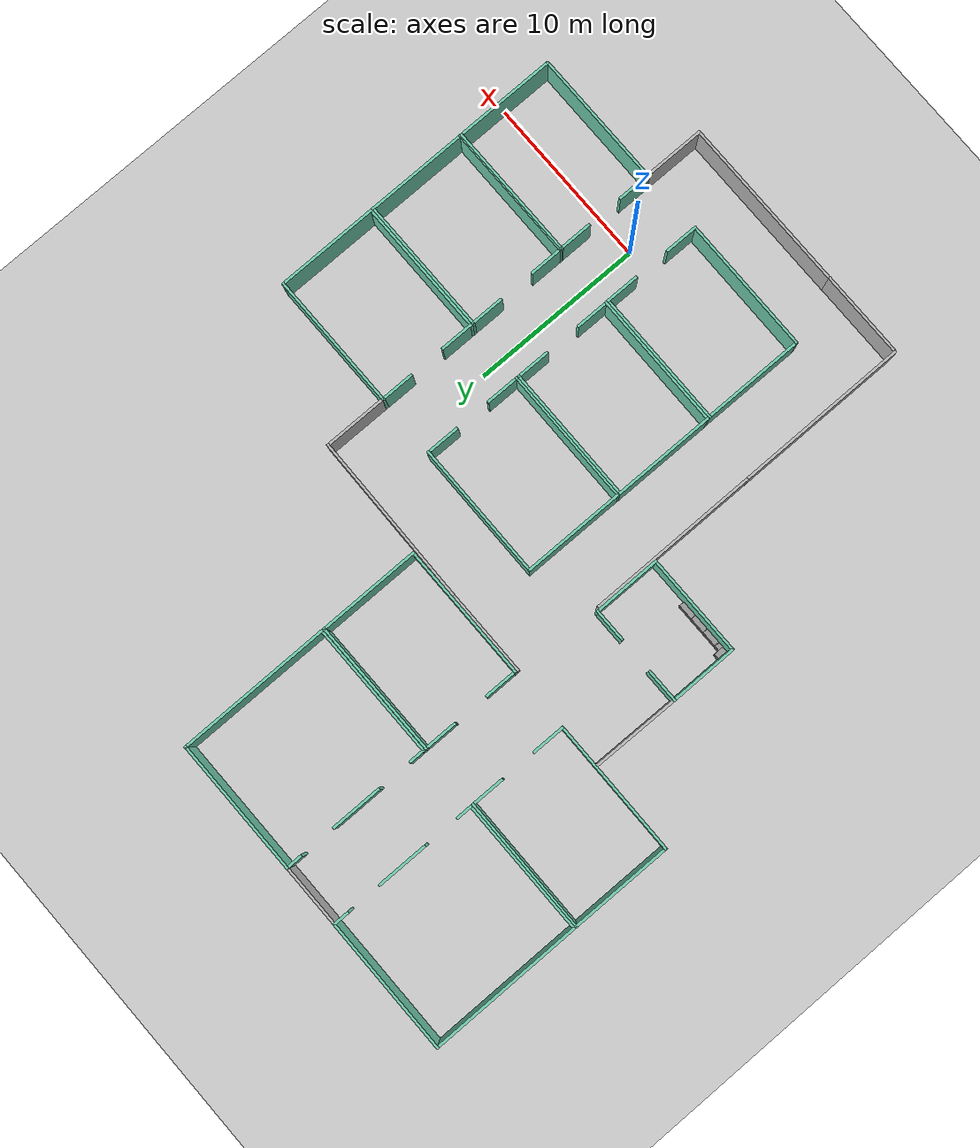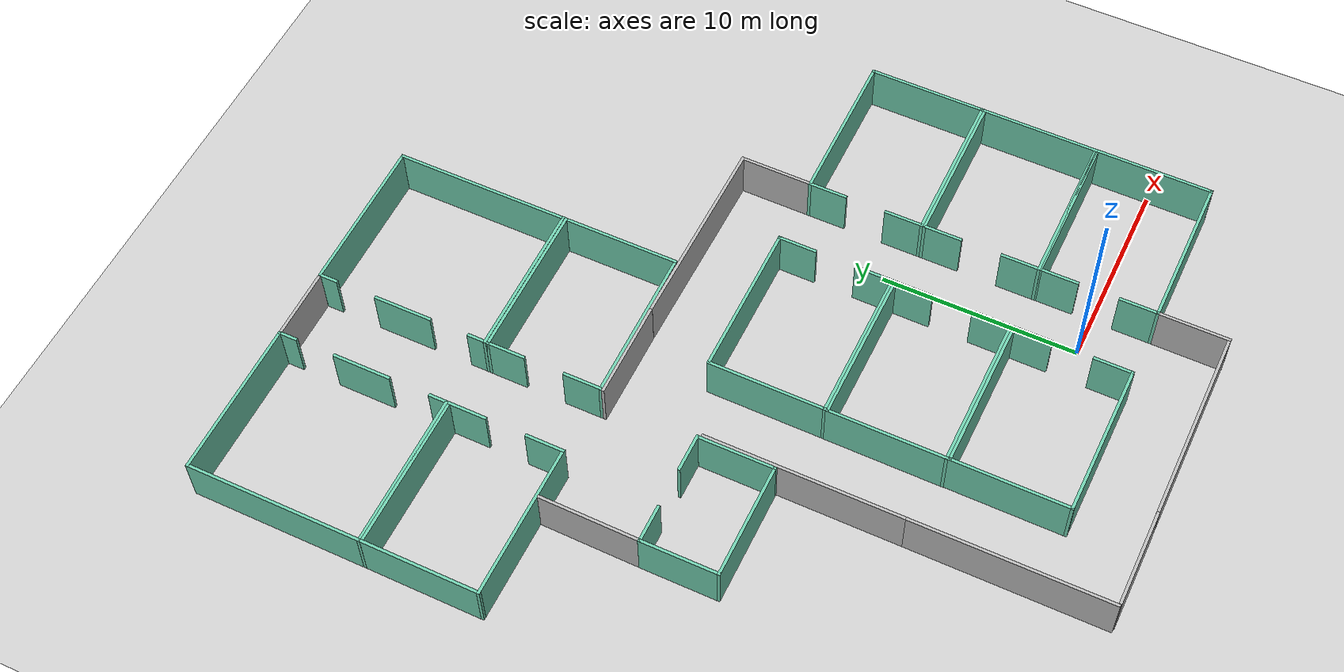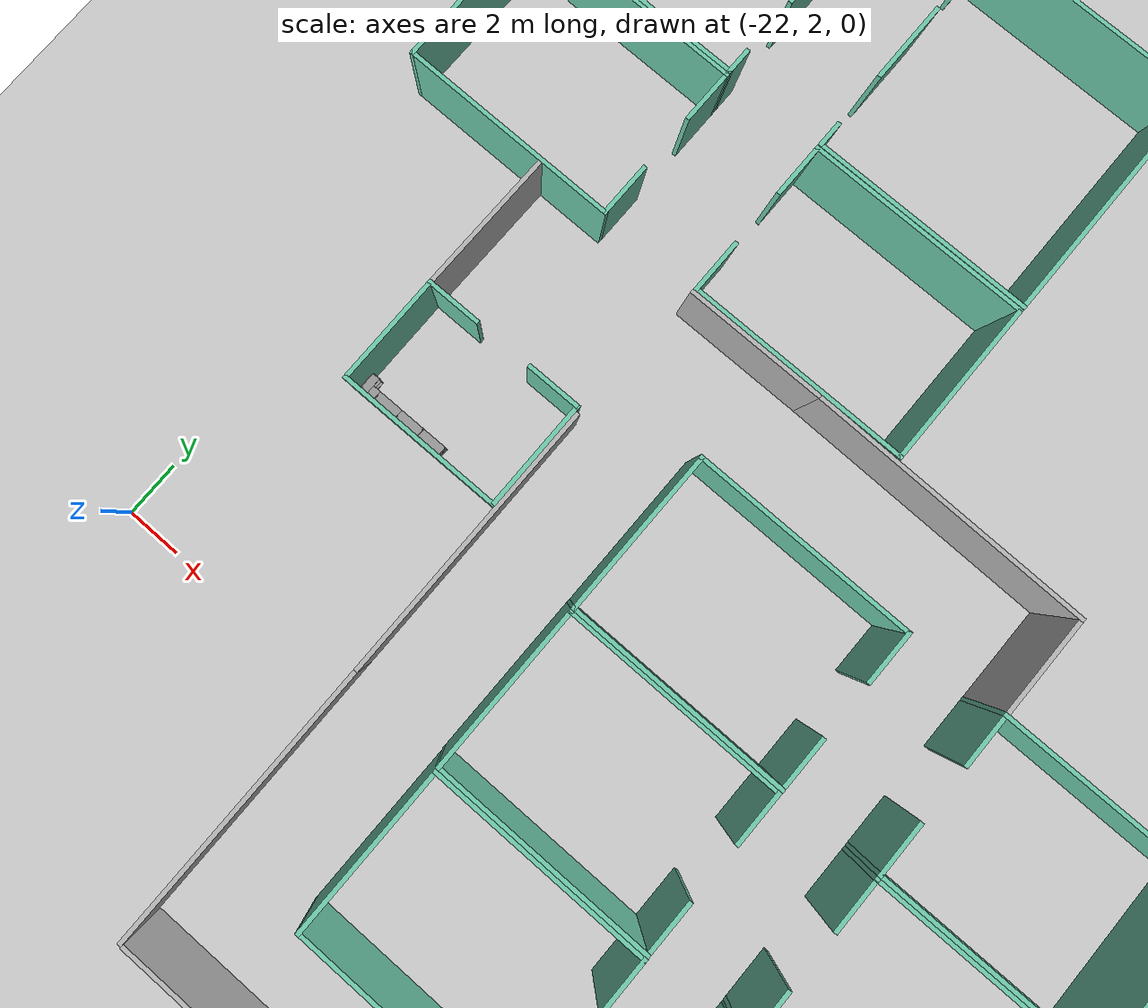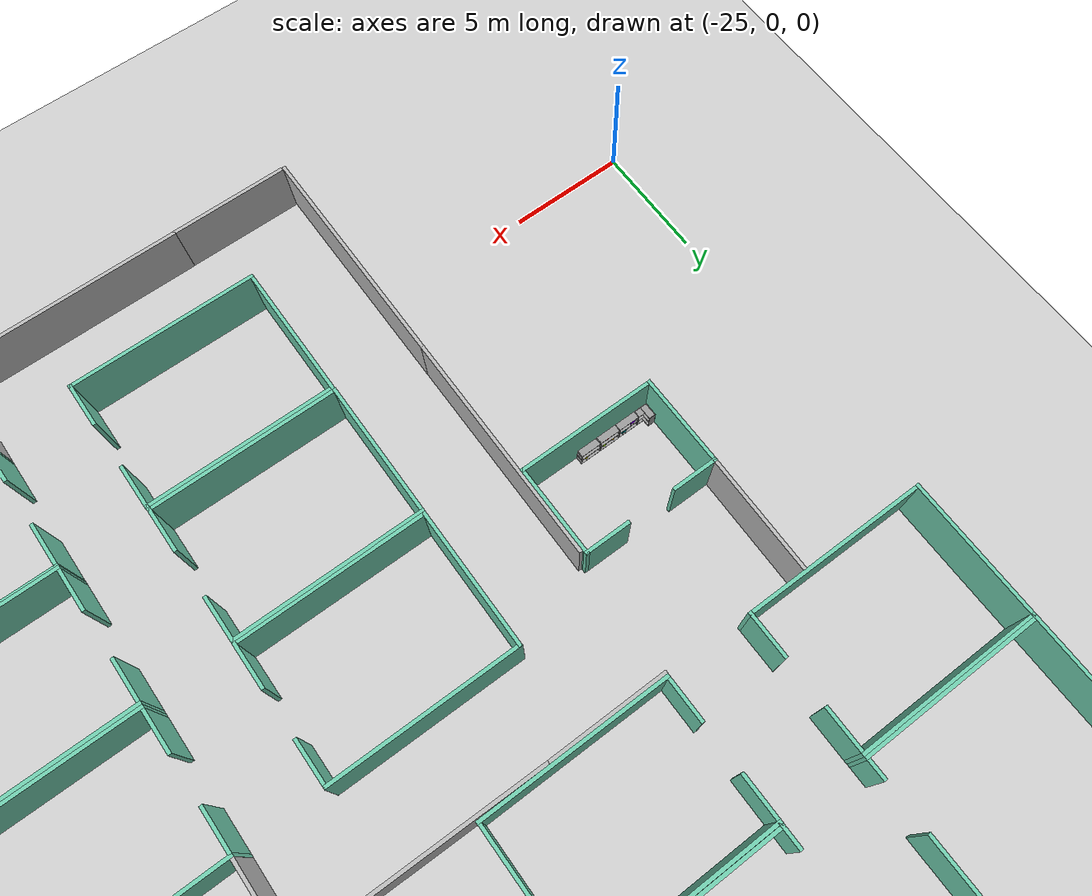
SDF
<sdf version="1.7">
 <world name="hospital">
  <light name="sun" type="directional">
   <pose>0 0 10 0 -0 0</pose>
   <diffuse>0.8 0.8 0.8 1</diffuse>
   <specular>0.2 0.2 0.2 1</specular>
   <attenuation>
    <range>1000</range>
    <constant>0.9</constant>
    <linear>0.01</linear>
    <quadratic>0.001</quadratic>
   </attenuation>
   <direction>-0.5 0.1 -0.9</direction>
   <spot><inner_angle>0</inner_angle><outer_angle>0</outer_angle><falloff>0</falloff></spot>
  </light>
  <model name="ground_plane">
   <static>1</static>
   <link name="link">
    <collision name="collision">
     <geometry><plane><normal>0 0 1</normal><size>100 100</size></plane></geometry>
     <surface>
      <contact><collide_bitmask>65535</collide_bitmask></contact>
      <friction><ode><mu>100</mu><mu2>50</mu2></ode></friction>
     </surface>
    </collision>
    <visual name="visual">
     <cast_shadows>0</cast_shadows>
     <geometry><plane><normal>0 0 1</normal><size>100 100</size></plane></geometry>
     <material>
      <script><uri>file://media/materials/scripts/gazebo.material</uri><name>Gazebo/Grey</name></script>
     </material>
    </visual>
   </link>
  </model>
  <gravity>0 0 -9.8</gravity>
  <magnetic_field>6e-06 2.3e-05 -4.2e-05</magnetic_field>
  <atmosphere type="adiabatic"/>
  <physics type="ode">
   <max_step_size>0.001</max_step_size>
   <real_time_factor>1</real_time_factor>
   <real_time_update_rate>1000</real_time_update_rate>
  </physics>
  <scene><ambient>0.4 0.4 0.4 1</ambient><background>0.7 0.7 0.7 1</background><shadows>1</shadows></scene>
  <spherical_coordinates>
   <surface_model>EARTH_WGS84</surface_model>
   <latitude_deg>0</latitude_deg>
   <longitude_deg>0</longitude_deg>
   <elevation>0</elevation>
   <heading_deg>0</heading_deg>
  </spherical_coordinates>
  <model name="model.sdf">
   <pose>6.00187 0.00802 0 0 -0 0</pose>
   <link name="Wall_0">
    <collision name="Wall_0_Collision">
     <geometry><box><size>8 0.15 2.5</size></box></geometry>
     <pose>0 0 1.25 0 -0 0</pose>
    </collision>
    <visual name="Wall_0_Visual">
     <pose>0 0 1.25 0 -0 0</pose>
     <geometry><box><size>8 0.15 2.5</size></box></geometry>
     <material>
      <script><uri>file://media/materials/scripts/gazebo.material</uri><name>Gazebo/Grey</name></script>
      <ambient>0.435294 0.796078 0.67451 1</ambient>
     </material>
     <meta><layer>0</layer></meta>
    </visual>
    <pose>-0 -2.925 0 0 -0 0</pose>
   </link>
   <link name="Wall_2">
    <collision name="Wall_2_Collision">
     <geometry><box><size>6 0.15 2.5</size></box></geometry>
     <pose>0 0 1.25 0 -0 0</pose>
    </collision>
    <visual name="Wall_2_Visual">
     <pose>0 0 1.25 0 -0 0</pose>
     <geometry><box><size>6 0.15 2.5</size></box></geometry>
     <material>
      <script><uri>file://media/materials/scripts/gazebo.material</uri><name>Gazebo/Grey</name></script>
      <ambient>0.435294 0.796078 0.67451 1</ambient>
     </material>
     <meta><layer>0</layer></meta>
    </visual>
    <pose>3.925 0 0 0 -0 1.5708</pose>
   </link>
   <link name="Wall_5">
    <collision name="Wall_5_Collision">
     <geometry><box><size>8 0.15 2.5</size></box></geometry>
     <pose>0 0 1.25 0 -0 0</pose>
    </collision>
    <visual name="Wall_5_Visual">
     <pose>0 0 1.25 0 -0 0</pose>
     <geometry><box><size>8 0.15 2.5</size></box></geometry>
     <material>
      <script><uri>file://media/materials/scripts/gazebo.material</uri><name>Gazebo/Grey</name></script>
      <ambient>0.435294 0.796078 0.67451 1</ambient>
     </material>
     <meta><layer>0</layer></meta>
    </visual>
    <pose>-0 2.925 0 0 -0 3.14159</pose>
   </link>
   <link name="Wall_6">
    <collision name="Wall_6_Collision">
     <geometry><box><size>2 0.15 2.5</size></box></geometry>
     <pose>0 0 1.25 0 -0 0</pose>
    </collision>
    <visual name="Wall_6_Visual">
     <pose>0 0 1.25 0 -0 0</pose>
     <geometry><box><size>2 0.15 2.5</size></box></geometry>
     <material>
      <script><uri>file://media/materials/scripts/gazebo.material</uri><name>Gazebo/Grey</name></script>
      <ambient>0.435294 0.796078 0.67451 1</ambient>
     </material>
     <meta><layer>0</layer></meta>
    </visual>
    <pose>-3.925 2 0 0 -0 -1.5708</pose>
   </link>
   <link name="Wall_8">
    <collision name="Wall_8_Collision">
     <geometry><box><size>2 0.15 2.5</size></box></geometry>
     <pose>0 0 1.25 0 -0 0</pose>
    </collision>
    <visual name="Wall_8_Visual">
     <pose>0 0 1.25 0 -0 0</pose>
     <geometry><box><size>2 0.15 2.5</size></box></geometry>
     <material>
      <script><uri>file://media/materials/scripts/gazebo.material</uri><name>Gazebo/Grey</name></script>
      <ambient>0.435294 0.796078 0.67451 1</ambient>
     </material>
     <meta><layer>0</layer></meta>
    </visual>
    <pose>-3.925 -2 0 0 -0 1.5708</pose>
   </link>
   <static>1</static>
  </model>
  <model name="model.sdf_0">
   <pose>5.99464 5.93809 0 0 -0 0</pose>
   <link name="Wall_0">
    <collision name="Wall_0_Collision">
     <geometry><box><size>8 0.15 2.5</size></box></geometry>
     <pose>0 0 1.25 0 -0 0</pose>
    </collision>
    <visual name="Wall_0_Visual">
     <pose>0 0 1.25 0 -0 0</pose>
     <geometry><box><size>8 0.15 2.5</size></box></geometry>
     <material>
      <script><uri>file://media/materials/scripts/gazebo.material</uri><name>Gazebo/Grey</name></script>
      <ambient>0.435294 0.796078 0.67451 1</ambient>
     </material>
     <meta><layer>0</layer></meta>
    </visual>
    <pose>-0 -2.925 0 0 -0 0</pose>
   </link>
   <link name="Wall_2">
    <collision name="Wall_2_Collision">
     <geometry><box><size>6 0.15 2.5</size></box></geometry>
     <pose>0 0 1.25 0 -0 0</pose>
    </collision>
    <visual name="Wall_2_Visual">
     <pose>0 0 1.25 0 -0 0</pose>
     <geometry><box><size>6 0.15 2.5</size></box></geometry>
     <material>
      <script><uri>file://media/materials/scripts/gazebo.material</uri><name>Gazebo/Grey</name></script>
      <ambient>0.435294 0.796078 0.67451 1</ambient>
     </material>
     <meta><layer>0</layer></meta>
    </visual>
    <pose>3.925 0 0 0 -0 1.5708</pose>
   </link>
   <link name="Wall_5">
    <collision name="Wall_5_Collision">
     <geometry><box><size>8 0.15 2.5</size></box></geometry>
     <pose>0 0 1.25 0 -0 0</pose>
    </collision>
    <visual name="Wall_5_Visual">
     <pose>0 0 1.25 0 -0 0</pose>
     <geometry><box><size>8 0.15 2.5</size></box></geometry>
     <material>
      <script><uri>file://media/materials/scripts/gazebo.material</uri><name>Gazebo/Grey</name></script>
      <ambient>0.435294 0.796078 0.67451 1</ambient>
     </material>
     <meta><layer>0</layer></meta>
    </visual>
    <pose>-0 2.925 0 0 -0 3.14159</pose>
   </link>
   <link name="Wall_6">
    <collision name="Wall_6_Collision">
     <geometry><box><size>2 0.15 2.5</size></box></geometry>
     <pose>0 0 1.25 0 -0 0</pose>
    </collision>
    <visual name="Wall_6_Visual">
     <pose>0 0 1.25 0 -0 0</pose>
     <geometry><box><size>2 0.15 2.5</size></box></geometry>
     <material>
      <script><uri>file://media/materials/scripts/gazebo.material</uri><name>Gazebo/Grey</name></script>
      <ambient>0.435294 0.796078 0.67451 1</ambient>
     </material>
     <meta><layer>0</layer></meta>
    </visual>
    <pose>-3.925 2 0 0 -0 -1.5708</pose>
   </link>
   <link name="Wall_8">
    <collision name="Wall_8_Collision">
     <geometry><box><size>2 0.15 2.5</size></box></geometry>
     <pose>0 0 1.25 0 -0 0</pose>
    </collision>
    <visual name="Wall_8_Visual">
     <pose>0 0 1.25 0 -0 0</pose>
     <geometry><box><size>2 0.15 2.5</size></box></geometry>
     <material>
      <script><uri>file://media/materials/scripts/gazebo.material</uri><name>Gazebo/Grey</name></script>
      <ambient>0.435294 0.796078 0.67451 1</ambient>
     </material>
     <meta><layer>0</layer></meta>
    </visual>
    <pose>-3.925 -2 0 0 -0 1.5708</pose>
   </link>
   <static>1</static>
  </model>
  <model name="model.sdf_1">
   <pose>5.99492 11.9339 0 0 -0 0</pose>
   <link name="Wall_0">
    <collision name="Wall_0_Collision">
     <geometry><box><size>8 0.15 2.5</size></box></geometry>
     <pose>0 0 1.25 0 -0 0</pose>
    </collision>
    <visual name="Wall_0_Visual">
     <pose>0 0 1.25 0 -0 0</pose>
     <geometry><box><size>8 0.15 2.5</size></box></geometry>
     <material>
      <script><uri>file://media/materials/scripts/gazebo.material</uri><name>Gazebo/Grey</name></script>
      <ambient>0.435294 0.796078 0.67451 1</ambient>
     </material>
     <meta><layer>0</layer></meta>
    </visual>
    <pose>-0 -2.925 0 0 -0 0</pose>
   </link>
   <link name="Wall_2">
    <collision name="Wall_2_Collision">
     <geometry><box><size>6 0.15 2.5</size></box></geometry>
     <pose>0 0 1.25 0 -0 0</pose>
    </collision>
    <visual name="Wall_2_Visual">
     <pose>0 0 1.25 0 -0 0</pose>
     <geometry><box><size>6 0.15 2.5</size></box></geometry>
     <material>
      <script><uri>file://media/materials/scripts/gazebo.material</uri><name>Gazebo/Grey</name></script>
      <ambient>0.435294 0.796078 0.67451 1</ambient>
     </material>
     <meta><layer>0</layer></meta>
    </visual>
    <pose>3.925 0 0 0 -0 1.5708</pose>
   </link>
   <link name="Wall_5">
    <collision name="Wall_5_Collision">
     <geometry><box><size>8 0.15 2.5</size></box></geometry>
     <pose>0 0 1.25 0 -0 0</pose>
    </collision>
    <visual name="Wall_5_Visual">
     <pose>0 0 1.25 0 -0 0</pose>
     <geometry><box><size>8 0.15 2.5</size></box></geometry>
     <material>
      <script><uri>file://media/materials/scripts/gazebo.material</uri><name>Gazebo/Grey</name></script>
      <ambient>0.435294 0.796078 0.67451 1</ambient>
     </material>
     <meta><layer>0</layer></meta>
    </visual>
    <pose>-0 2.925 0 0 -0 3.14159</pose>
   </link>
   <link name="Wall_6">
    <collision name="Wall_6_Collision">
     <geometry><box><size>2 0.15 2.5</size></box></geometry>
     <pose>0 0 1.25 0 -0 0</pose>
    </collision>
    <visual name="Wall_6_Visual">
     <pose>0 0 1.25 0 -0 0</pose>
     <geometry><box><size>2 0.15 2.5</size></box></geometry>
     <material>
      <script><uri>file://media/materials/scripts/gazebo.material</uri><name>Gazebo/Grey</name></script>
      <ambient>0.435294 0.796078 0.67451 1</ambient>
     </material>
     <meta><layer>0</layer></meta>
    </visual>
    <pose>-3.925 2 0 0 -0 -1.5708</pose>
   </link>
   <link name="Wall_8">
    <collision name="Wall_8_Collision">
     <geometry><box><size>2 0.15 2.5</size></box></geometry>
     <pose>0 0 1.25 0 -0 0</pose>
    </collision>
    <visual name="Wall_8_Visual">
     <pose>0 0 1.25 0 -0 0</pose>
     <geometry><box><size>2 0.15 2.5</size></box></geometry>
     <material>
      <script><uri>file://media/materials/scripts/gazebo.material</uri><name>Gazebo/Grey</name></script>
      <ambient>0.435294 0.796078 0.67451 1</ambient>
     </material>
     <meta><layer>0</layer></meta>
    </visual>
    <pose>-3.925 -2 0 0 -0 1.5708</pose>
   </link>
   <static>1</static>
  </model>
  <model name="wall_3_5">
   <static>1</static>
   <link name="link">
    <pose>0 0 1.25 0 -0 0</pose>
    <collision name="collision">
     <geometry><box><size>3.5 0.15 2.5</size></box></geometry>
     <surface>
      <contact>
       <collide_without_contact>1</collide_without_contact>
       <collide_without_contact_bitmask>2</collide_without_contact_bitmask>
      </contact>
     </surface>
    </collision>
    <visual name="visual">
     <cast_shadows>0</cast_shadows>
     <geometry><box><size>3.5 0.15 2.5</size></box></geometry>
     <material>
      <script>
       <uri>model://cutout_wall/materials/scripts</uri>
       <uri>model://cutout_wall/materials/textures</uri>
       <name>drc_practice/cutout_wall</name>
      </script>
     </material>
    </visual>
    <sensor name="mud_contact" type="contact">
     <always_on>1</always_on>
     <update_rate>1000</update_rate>
     <contact><collision>collision</collision><topic>__default_topic__</topic></contact>
    </sensor>
   </link>
   <plugin name="gazebo_mud" filename="libMudPlugin.so">
    <contact_sensor_name>link/mud_contact</contact_sensor_name>
    <stiffness>0.0</stiffness>
    <damping>40.0</damping>
    <contact_surface_bitmask>2</contact_surface_bitmask>
    <link_name>drill::link</link_name>
   </plugin>
   <pose>2.07112 -4.73808 -0 0 -0 1.56806</pose>
  </model>
  <model name="model.sdf_2">
   <pose>-5.47704 -0.011767 0 0 -0 3.13762</pose>
   <link name="Wall_0">
    <collision name="Wall_0_Collision">
     <geometry><box><size>8 0.15 2.5</size></box></geometry>
     <pose>0 0 1.25 0 -0 0</pose>
    </collision>
    <visual name="Wall_0_Visual">
     <pose>0 0 1.25 0 -0 0</pose>
     <geometry><box><size>8 0.15 2.5</size></box></geometry>
     <material>
      <script><uri>file://media/materials/scripts/gazebo.material</uri><name>Gazebo/Grey</name></script>
      <ambient>0.435294 0.796078 0.67451 1</ambient>
     </material>
     <meta><layer>0</layer></meta>
    </visual>
    <pose>-0 -2.925 0 0 -0 0</pose>
   </link>
   <link name="Wall_2">
    <collision name="Wall_2_Collision">
     <geometry><box><size>6 0.15 2.5</size></box></geometry>
     <pose>0 0 1.25 0 -0 0</pose>
    </collision>
    <visual name="Wall_2_Visual">
     <pose>0 0 1.25 0 -0 0</pose>
     <geometry><box><size>6 0.15 2.5</size></box></geometry>
     <material>
      <script><uri>file://media/materials/scripts/gazebo.material</uri><name>Gazebo/Grey</name></script>
      <ambient>0.435294 0.796078 0.67451 1</ambient>
     </material>
     <meta><layer>0</layer></meta>
    </visual>
    <pose>3.925 0 0 0 -0 1.5708</pose>
   </link>
   <link name="Wall_5">
    <collision name="Wall_5_Collision">
     <geometry><box><size>8 0.15 2.5</size></box></geometry>
     <pose>0 0 1.25 0 -0 0</pose>
    </collision>
    <visual name="Wall_5_Visual">
     <pose>0 0 1.25 0 -0 0</pose>
     <geometry><box><size>8 0.15 2.5</size></box></geometry>
     <material>
      <script><uri>file://media/materials/scripts/gazebo.material</uri><name>Gazebo/Grey</name></script>
      <ambient>0.435294 0.796078 0.67451 1</ambient>
     </material>
     <meta><layer>0</layer></meta>
    </visual>
    <pose>-0 2.925 0 0 -0 3.14159</pose>
   </link>
   <link name="Wall_6">
    <collision name="Wall_6_Collision">
     <geometry><box><size>2 0.15 2.5</size></box></geometry>
     <pose>0 0 1.25 0 -0 0</pose>
    </collision>
    <visual name="Wall_6_Visual">
     <pose>0 0 1.25 0 -0 0</pose>
     <geometry><box><size>2 0.15 2.5</size></box></geometry>
     <material>
      <script><uri>file://media/materials/scripts/gazebo.material</uri><name>Gazebo/Grey</name></script>
      <ambient>0.435294 0.796078 0.67451 1</ambient>
     </material>
     <meta><layer>0</layer></meta>
    </visual>
    <pose>-3.925 2 0 0 -0 -1.5708</pose>
   </link>
   <link name="Wall_8">
    <collision name="Wall_8_Collision">
     <geometry><box><size>2 0.15 2.5</size></box></geometry>
     <pose>0 0 1.25 0 -0 0</pose>
    </collision>
    <visual name="Wall_8_Visual">
     <pose>0 0 1.25 0 -0 0</pose>
     <geometry><box><size>2 0.15 2.5</size></box></geometry>
     <material>
      <script><uri>file://media/materials/scripts/gazebo.material</uri><name>Gazebo/Grey</name></script>
      <ambient>0.435294 0.796078 0.67451 1</ambient>
     </material>
     <meta><layer>0</layer></meta>
    </visual>
    <pose>-3.925 -2 0 0 -0 1.5708</pose>
   </link>
   <static>1</static>
  </model>
  <model name="model.sdf_2_clone">
   <pose>-5.47026 5.98318 0 0 -0 3.13762</pose>
   <link name="Wall_0">
    <collision name="Wall_0_Collision">
     <geometry><box><size>8 0.15 2.5</size></box></geometry>
     <pose>0 0 1.25 0 -0 0</pose>
    </collision>
    <visual name="Wall_0_Visual">
     <pose>0 0 1.25 0 -0 0</pose>
     <geometry><box><size>8 0.15 2.5</size></box></geometry>
     <material>
      <script><uri>file://media/materials/scripts/gazebo.material</uri><name>Gazebo/Grey</name></script>
      <ambient>0.435294 0.796078 0.67451 1</ambient>
     </material>
     <meta><layer>0</layer></meta>
    </visual>
    <pose>-0 -2.925 0 0 -0 0</pose>
   </link>
   <link name="Wall_2">
    <collision name="Wall_2_Collision">
     <geometry><box><size>6 0.15 2.5</size></box></geometry>
     <pose>0 0 1.25 0 -0 0</pose>
    </collision>
    <visual name="Wall_2_Visual">
     <pose>0 0 1.25 0 -0 0</pose>
     <geometry><box><size>6 0.15 2.5</size></box></geometry>
     <material>
      <script><uri>file://media/materials/scripts/gazebo.material</uri><name>Gazebo/Grey</name></script>
      <ambient>0.435294 0.796078 0.67451 1</ambient>
     </material>
     <meta><layer>0</layer></meta>
    </visual>
    <pose>3.925 0 0 0 -0 1.5708</pose>
   </link>
   <link name="Wall_5">
    <collision name="Wall_5_Collision">
     <geometry><box><size>8 0.15 2.5</size></box></geometry>
     <pose>0 0 1.25 0 -0 0</pose>
    </collision>
    <visual name="Wall_5_Visual">
     <pose>0 0 1.25 0 -0 0</pose>
     <geometry><box><size>8 0.15 2.5</size></box></geometry>
     <material>
      <script><uri>file://media/materials/scripts/gazebo.material</uri><name>Gazebo/Grey</name></script>
      <ambient>0.435294 0.796078 0.67451 1</ambient>
     </material>
     <meta><layer>0</layer></meta>
    </visual>
    <pose>-0 2.925 0 0 -0 3.14159</pose>
   </link>
   <link name="Wall_6">
    <collision name="Wall_6_Collision">
     <geometry><box><size>2 0.15 2.5</size></box></geometry>
     <pose>0 0 1.25 0 -0 0</pose>
    </collision>
    <visual name="Wall_6_Visual">
     <pose>0 0 1.25 0 -0 0</pose>
     <geometry><box><size>2 0.15 2.5</size></box></geometry>
     <material>
      <script><uri>file://media/materials/scripts/gazebo.material</uri><name>Gazebo/Grey</name></script>
      <ambient>0.435294 0.796078 0.67451 1</ambient>
     </material>
     <meta><layer>0</layer></meta>
    </visual>
    <pose>-3.925 2 0 0 -0 -1.5708</pose>
   </link>
   <link name="Wall_8">
    <collision name="Wall_8_Collision">
     <geometry><box><size>2 0.15 2.5</size></box></geometry>
     <pose>0 0 1.25 0 -0 0</pose>
    </collision>
    <visual name="Wall_8_Visual">
     <pose>0 0 1.25 0 -0 0</pose>
     <geometry><box><size>2 0.15 2.5</size></box></geometry>
     <material>
      <script><uri>file://media/materials/scripts/gazebo.material</uri><name>Gazebo/Grey</name></script>
      <ambient>0.435294 0.796078 0.67451 1</ambient>
     </material>
     <meta><layer>0</layer></meta>
    </visual>
    <pose>-3.925 -2 0 0 -0 1.5708</pose>
   </link>
   <static>1</static>
  </model>
  <model name="model.sdf_2_clone_clone">
   <pose>-5.44042 11.9649 0 0 -0 3.13762</pose>
   <link name="Wall_0">
    <collision name="Wall_0_Collision">
     <geometry><box><size>8 0.15 2.5</size></box></geometry>
     <pose>0 0 1.25 0 -0 0</pose>
    </collision>
    <visual name="Wall_0_Visual">
     <pose>0 0 1.25 0 -0 0</pose>
     <geometry><box><size>8 0.15 2.5</size></box></geometry>
     <material>
      <script><uri>file://media/materials/scripts/gazebo.material</uri><name>Gazebo/Grey</name></script>
      <ambient>0.435294 0.796078 0.67451 1</ambient>
     </material>
     <meta><layer>0</layer></meta>
    </visual>
    <pose>-0 -2.925 0 0 -0 0</pose>
   </link>
   <link name="Wall_2">
    <collision name="Wall_2_Collision">
     <geometry><box><size>6 0.15 2.5</size></box></geometry>
     <pose>0 0 1.25 0 -0 0</pose>
    </collision>
    <visual name="Wall_2_Visual">
     <pose>0 0 1.25 0 -0 0</pose>
     <geometry><box><size>6 0.15 2.5</size></box></geometry>
     <material>
      <script><uri>file://media/materials/scripts/gazebo.material</uri><name>Gazebo/Grey</name></script>
      <ambient>0.435294 0.796078 0.67451 1</ambient>
     </material>
     <meta><layer>0</layer></meta>
    </visual>
    <pose>3.925 0 0 0 -0 1.5708</pose>
   </link>
   <link name="Wall_5">
    <collision name="Wall_5_Collision">
     <geometry><box><size>8 0.15 2.5</size></box></geometry>
     <pose>0 0 1.25 0 -0 0</pose>
    </collision>
    <visual name="Wall_5_Visual">
     <pose>0 0 1.25 0 -0 0</pose>
     <geometry><box><size>8 0.15 2.5</size></box></geometry>
     <material>
      <script><uri>file://media/materials/scripts/gazebo.material</uri><name>Gazebo/Grey</name></script>
      <ambient>0.435294 0.796078 0.67451 1</ambient>
     </material>
     <meta><layer>0</layer></meta>
    </visual>
    <pose>-0 2.925 0 0 -0 3.14159</pose>
   </link>
   <link name="Wall_6">
    <collision name="Wall_6_Collision">
     <geometry><box><size>2 0.15 2.5</size></box></geometry>
     <pose>0 0 1.25 0 -0 0</pose>
    </collision>
    <visual name="Wall_6_Visual">
     <pose>0 0 1.25 0 -0 0</pose>
     <geometry><box><size>2 0.15 2.5</size></box></geometry>
     <material>
      <script><uri>file://media/materials/scripts/gazebo.material</uri><name>Gazebo/Grey</name></script>
      <ambient>0.435294 0.796078 0.67451 1</ambient>
     </material>
     <meta><layer>0</layer></meta>
    </visual>
    <pose>-3.925 2 0 0 -0 -1.5708</pose>
   </link>
   <link name="Wall_8">
    <collision name="Wall_8_Collision">
     <geometry><box><size>2 0.15 2.5</size></box></geometry>
     <pose>0 0 1.25 0 -0 0</pose>
    </collision>
    <visual name="Wall_8_Visual">
     <pose>0 0 1.25 0 -0 0</pose>
     <geometry><box><size>2 0.15 2.5</size></box></geometry>
     <material>
      <script><uri>file://media/materials/scripts/gazebo.material</uri><name>Gazebo/Grey</name></script>
      <ambient>0.435294 0.796078 0.67451 1</ambient>
     </material>
     <meta><layer>0</layer></meta>
    </visual>
    <pose>-3.925 -2 0 0 -0 1.5708</pose>
   </link>
   <static>1</static>
  </model>
  <model name="wall_10">
   <static>1</static>
   <link name="link">
    <pose>0 0 1.25 0 -0 0</pose>
    <collision name="collision">
     <geometry><box><size>10 0.15 2.5</size></box></geometry>
     <surface>
      <contact>
       <collide_without_contact>1</collide_without_contact>
       <collide_without_contact_bitmask>2</collide_without_contact_bitmask>
      </contact>
     </surface>
    </collision>
    <visual name="visual">
     <cast_shadows>0</cast_shadows>
     <geometry><box><size>10 0.15 2.5</size></box></geometry>
     <material>
      <script>
       <uri>model://cutout_wall/materials/scripts</uri>
       <uri>model://cutout_wall/materials/textures</uri>
       <name>drc_practice/cutout_wall</name>
      </script>
     </material>
    </visual>
    <sensor name="mud_contact" type="contact">
     <always_on>1</always_on>
     <update_rate>1000</update_rate>
     <contact><collision>collision</collision><topic>__default_topic__</topic></contact>
    </sensor>
   </link>
   <plugin name="gazebo_mud" filename="libMudPlugin.so">
    <contact_sensor_name>link/mud_contact</contact_sensor_name>
    <stiffness>0.0</stiffness>
    <damping>40.0</damping>
    <contact_surface_bitmask>2</contact_surface_bitmask>
    <link_name>drill::link</link_name>
   </plugin>
   <pose>-3.00199 -6.40567 0 0 -0 0</pose>
  </model>
  <model name="wall_10_0">
   <static>1</static>
   <link name="link">
    <pose>0 0 1.25 0 -0 0</pose>
    <collision name="collision">
     <geometry><box><size>10 0.15 2.5</size></box></geometry>
     <surface>
      <contact>
       <collide_without_contact>1</collide_without_contact>
       <collide_without_contact_bitmask>2</collide_without_contact_bitmask>
      </contact>
     </surface>
    </collision>
    <visual name="visual">
     <cast_shadows>0</cast_shadows>
     <geometry><box><size>10 0.15 2.5</size></box></geometry>
     <material>
      <script>
       <uri>model://cutout_wall/materials/scripts</uri>
       <uri>model://cutout_wall/materials/textures</uri>
       <name>drc_practice/cutout_wall</name>
      </script>
     </material>
    </visual>
    <sensor name="mud_contact" type="contact">
     <always_on>1</always_on>
     <update_rate>1000</update_rate>
     <contact><collision>collision</collision><topic>__default_topic__</topic></contact>
    </sensor>
   </link>
   <plugin name="gazebo_mud" filename="libMudPlugin.so">
    <contact_sensor_name>link/mud_contact</contact_sensor_name>
    <stiffness>0.0</stiffness>
    <damping>40.0</damping>
    <contact_surface_bitmask>2</contact_surface_bitmask>
    <link_name>drill::link</link_name>
   </plugin>
   <pose>-13.0332 -1.45494 0 0 0 -1.57214</pose>
  </model>
  <model name="wall_5">
   <static>1</static>
   <link name="link">
    <pose>0 0 1.25 0 -0 0</pose>
    <collision name="collision">
     <geometry><box><size>5 0.15 2.5</size></box></geometry>
     <surface>
      <contact>
       <collide_without_contact>1</collide_without_contact>
       <collide_without_contact_bitmask>2</collide_without_contact_bitmask>
      </contact>
     </surface>
    </collision>
    <visual name="visual">
     <cast_shadows>0</cast_shadows>
     <geometry><box><size>5 0.15 2.5</size></box></geometry>
     <material>
      <script>
       <uri>model://cutout_wall/materials/scripts</uri>
       <uri>model://cutout_wall/materials/textures</uri>
       <name>drc_practice/cutout_wall</name>
      </script>
     </material>
    </visual>
    <sensor name="mud_contact" type="contact">
     <always_on>1</always_on>
     <update_rate>1000</update_rate>
     <contact><collision>collision</collision><topic>__default_topic__</topic></contact>
    </sensor>
   </link>
   <plugin name="gazebo_mud" filename="libMudPlugin.so">
    <contact_sensor_name>link/mud_contact</contact_sensor_name>
    <stiffness>0.0</stiffness>
    <damping>40.0</damping>
    <contact_surface_bitmask>2</contact_surface_bitmask>
    <link_name>drill::link</link_name>
   </plugin>
   <pose>-10.4583 -6.41458 0 0 -0 0</pose>
  </model>
  <model name="wall_10_0_clone">
   <static>1</static>
   <link name="link">
    <pose>0 0 1.25 0 -0 0</pose>
    <collision name="collision">
     <geometry><box><size>10 0.15 2.5</size></box></geometry>
     <surface>
      <contact>
       <collide_without_contact>1</collide_without_contact>
       <collide_without_contact_bitmask>2</collide_without_contact_bitmask>
      </contact>
     </surface>
    </collision>
    <visual name="visual">
     <cast_shadows>0</cast_shadows>
     <geometry><box><size>10 0.15 2.5</size></box></geometry>
     <material>
      <script>
       <uri>model://cutout_wall/materials/scripts</uri>
       <uri>model://cutout_wall/materials/textures</uri>
       <name>drc_practice/cutout_wall</name>
      </script>
     </material>
    </visual>
    <sensor name="mud_contact" type="contact">
     <always_on>1</always_on>
     <update_rate>1000</update_rate>
     <contact><collision>collision</collision><topic>__default_topic__</topic></contact>
    </sensor>
   </link>
   <plugin name="gazebo_mud" filename="libMudPlugin.so">
    <contact_sensor_name>link/mud_contact</contact_sensor_name>
    <stiffness>0.0</stiffness>
    <damping>40.0</damping>
    <contact_surface_bitmask>2</contact_surface_bitmask>
    <link_name>drill::link</link_name>
   </plugin>
   <pose>-13.02 8.53758 0 0 0 -1.57214</pose>
  </model>
  <model name="wall_3_5_clone">
   <static>1</static>
   <link name="link">
    <pose>0 0 1.25 0 -0 0</pose>
    <collision name="collision">
     <geometry><box><size>3.5 0.15 2.5</size></box></geometry>
     <surface>
      <contact>
       <collide_without_contact>1</collide_without_contact>
       <collide_without_contact_bitmask>2</collide_without_contact_bitmask>
      </contact>
     </surface>
    </collision>
    <visual name="visual">
     <cast_shadows>0</cast_shadows>
     <geometry><box><size>3.5 0.15 2.5</size></box></geometry>
     <material>
      <script>
       <uri>model://cutout_wall/materials/scripts</uri>
       <uri>model://cutout_wall/materials/textures</uri>
       <name>drc_practice/cutout_wall</name>
      </script>
     </material>
    </visual>
    <sensor name="mud_contact" type="contact">
     <always_on>1</always_on>
     <update_rate>1000</update_rate>
     <contact><collision>collision</collision><topic>__default_topic__</topic></contact>
    </sensor>
   </link>
   <plugin name="gazebo_mud" filename="libMudPlugin.so">
    <contact_sensor_name>link/mud_contact</contact_sensor_name>
    <stiffness>0.0</stiffness>
    <damping>40.0</damping>
    <contact_surface_bitmask>2</contact_surface_bitmask>
    <link_name>drill::link</link_name>
   </plugin>
   <pose>2.08091 16.6634 -0 0 -0 1.56806</pose>
  </model>
  <model name="wall_10_clone">
   <static>1</static>
   <link name="link">
    <pose>0 0 1.25 0 -0 0</pose>
    <collision name="collision">
     <geometry><box><size>10 0.15 2.5</size></box></geometry>
     <surface>
      <contact>
       <collide_without_contact>1</collide_without_contact>
       <collide_without_contact_bitmask>2</collide_without_contact_bitmask>
      </contact>
     </surface>
    </collision>
    <visual name="visual">
     <cast_shadows>0</cast_shadows>
     <geometry><box><size>10 0.15 2.5</size></box></geometry>
     <material>
      <script>
       <uri>model://cutout_wall/materials/scripts</uri>
       <uri>model://cutout_wall/materials/textures</uri>
       <name>drc_practice/cutout_wall</name>
      </script>
     </material>
    </visual>
    <sensor name="mud_contact" type="contact">
     <always_on>1</always_on>
     <update_rate>1000</update_rate>
     <contact><collision>collision</collision><topic>__default_topic__</topic></contact>
    </sensor>
   </link>
   <plugin name="gazebo_mud" filename="libMudPlugin.so">
    <contact_sensor_name>link/mud_contact</contact_sensor_name>
    <stiffness>0.0</stiffness>
    <damping>40.0</damping>
    <contact_surface_bitmask>2</contact_surface_bitmask>
    <link_name>drill::link</link_name>
   </plugin>
   <pose>-2.83918 18.5508 -0 0 0 -0.014119</pose>
  </model>
  <model name="wall_5_clone">
   <static>1</static>
   <link name="link">
    <pose>0 0 1.25 0 -0 0</pose>
    <collision name="collision">
     <geometry><box><size>5 0.15 2.5</size></box></geometry>
     <surface>
      <contact>
       <collide_without_contact>1</collide_without_contact>
       <collide_without_contact_bitmask>2</collide_without_contact_bitmask>
      </contact>
     </surface>
    </collision>
    <visual name="visual">
     <cast_shadows>0</cast_shadows>
     <geometry><box><size>5 0.15 2.5</size></box></geometry>
     <material>
      <script>
       <uri>model://cutout_wall/materials/scripts</uri>
       <uri>model://cutout_wall/materials/textures</uri>
       <name>drc_practice/cutout_wall</name>
      </script>
     </material>
    </visual>
    <sensor name="mud_contact" type="contact">
     <always_on>1</always_on>
     <update_rate>1000</update_rate>
     <contact><collision>collision</collision><topic>__default_topic__</topic></contact>
    </sensor>
   </link>
   <plugin name="gazebo_mud" filename="libMudPlugin.so">
    <contact_sensor_name>link/mud_contact</contact_sensor_name>
    <stiffness>0.0</stiffness>
    <damping>40.0</damping>
    <contact_surface_bitmask>2</contact_surface_bitmask>
    <link_name>drill::link</link_name>
   </plugin>
   <pose>-10.3264 18.6222 0 0 -0 0</pose>
  </model>
  <model name="hospital_stroage_room">
   <pose>-16.0834 11.7449 0 0 -0 0</pose>
   <link name="Wall_0">
    <collision name="Wall_0_Collision">
     <geometry><box><size>6 0.15 2.5</size></box></geometry>
     <pose>0 0 1.25 0 -0 0</pose>
    </collision>
    <visual name="Wall_0_Visual">
     <pose>0 0 1.25 0 -0 0</pose>
     <geometry><box><size>6 0.15 2.5</size></box></geometry>
     <material>
      <script><uri>file://media/materials/scripts/gazebo.material</uri><name>Gazebo/Grey</name></script>
      <ambient>0.435294 0.796078 0.67451 1</ambient>
     </material>
     <meta><layer>0</layer></meta>
    </visual>
    <pose>-0 -1.925 0 0 -0 0</pose>
   </link>
   <link name="Wall_1">
    <collision name="Wall_1_Collision">
     <geometry><box><size>4 0.15 2.5</size></box></geometry>
     <pose>0 0 1.25 0 -0 0</pose>
    </collision>
    <visual name="Wall_1_Visual">
     <pose>0 0 1.25 0 -0 0</pose>
     <geometry><box><size>4 0.15 2.5</size></box></geometry>
     <material>
      <script><uri>file://media/materials/scripts/gazebo.material</uri><name>Gazebo/Grey</name></script>
      <ambient>0.435294 0.796078 0.67451 1</ambient>
     </material>
     <meta><layer>0</layer></meta>
    </visual>
    <pose>2.925 0 0 0 -0 1.5708</pose>
   </link>
   <link name="Wall_3">
    <collision name="Wall_3_Collision">
     <geometry><box><size>4 0.15 2.5</size></box></geometry>
     <pose>0 0 1.25 0 -0 0</pose>
    </collision>
    <visual name="Wall_3_Visual">
     <pose>0 0 1.25 0 -0 0</pose>
     <geometry><box><size>4 0.15 2.5</size></box></geometry>
     <material>
      <script><uri>file://media/materials/scripts/gazebo.material</uri><name>Gazebo/Grey</name></script>
      <ambient>0.435294 0.796078 0.67451 1</ambient>
     </material>
     <meta><layer>0</layer></meta>
    </visual>
    <pose>-2.925 0 0 0 -0 1.5708</pose>
   </link>
   <link name="Wall_4">
    <collision name="Wall_4_Collision">
     <geometry><box><size>2 0.15 2.5</size></box></geometry>
     <pose>0 0 1.25 0 -0 0</pose>
    </collision>
    <visual name="Wall_4_Visual">
     <pose>0 0 1.25 0 -0 0</pose>
     <geometry><box><size>2 0.15 2.5</size></box></geometry>
     <material>
      <script><uri>file://media/materials/scripts/gazebo.material</uri><name>Gazebo/Grey</name></script>
      <ambient>0.435294 0.796078 0.67451 1</ambient>
     </material>
     <meta><layer>0</layer></meta>
    </visual>
    <pose>-2 1.925 0 0 -0 0</pose>
   </link>
   <link name="Wall_6">
    <collision name="Wall_6_Collision">
     <geometry><box><size>2 0.15 2.5</size></box></geometry>
     <pose>0 0 1.25 0 -0 0</pose>
    </collision>
    <visual name="Wall_6_Visual">
     <pose>0 0 1.25 0 -0 0</pose>
     <geometry><box><size>2 0.15 2.5</size></box></geometry>
     <material>
      <script><uri>file://media/materials/scripts/gazebo.material</uri><name>Gazebo/Grey</name></script>
      <ambient>0.435294 0.796078 0.67451 1</ambient>
     </material>
     <meta><layer>0</layer></meta>
    </visual>
    <pose>2 1.925 0 0 -0 3.14159</pose>
   </link>
   <static>1</static>
  </model>
  <model name="model.sdf_clone">
   <pose>-8.82013 21.689 0 0 -0 0</pose>
   <link name="Wall_0">
    <collision name="Wall_0_Collision">
     <geometry><box><size>8 0.15 2.5</size></box></geometry>
     <pose>0 0 1.25 0 -0 0</pose>
    </collision>
    <visual name="Wall_0_Visual">
     <pose>0 0 1.25 0 -0 0</pose>
     <geometry><box><size>8 0.15 2.5</size></box></geometry>
     <material>
      <script><uri>file://media/materials/scripts/gazebo.material</uri><name>Gazebo/Grey</name></script>
      <ambient>0.435294 0.796078 0.67451 1</ambient>
     </material>
     <meta><layer>0</layer></meta>
    </visual>
    <pose>-0 -2.925 0 0 -0 0</pose>
   </link>
   <link name="Wall_2">
    <collision name="Wall_2_Collision">
     <geometry><box><size>6 0.15 2.5</size></box></geometry>
     <pose>0 0 1.25 0 -0 0</pose>
    </collision>
    <visual name="Wall_2_Visual">
     <pose>0 0 1.25 0 -0 0</pose>
     <geometry><box><size>6 0.15 2.5</size></box></geometry>
     <material>
      <script><uri>file://media/materials/scripts/gazebo.material</uri><name>Gazebo/Grey</name></script>
      <ambient>0.435294 0.796078 0.67451 1</ambient>
     </material>
     <meta><layer>0</layer></meta>
    </visual>
    <pose>3.925 0 0 0 -0 1.5708</pose>
   </link>
   <link name="Wall_5">
    <collision name="Wall_5_Collision">
     <geometry><box><size>8 0.15 2.5</size></box></geometry>
     <pose>0 0 1.25 0 -0 0</pose>
    </collision>
    <visual name="Wall_5_Visual">
     <pose>0 0 1.25 0 -0 0</pose>
     <geometry><box><size>8 0.15 2.5</size></box></geometry>
     <material>
      <script><uri>file://media/materials/scripts/gazebo.material</uri><name>Gazebo/Grey</name></script>
      <ambient>0.435294 0.796078 0.67451 1</ambient>
     </material>
     <meta><layer>0</layer></meta>
    </visual>
    <pose>-0 2.925 0 0 -0 3.14159</pose>
   </link>
   <link name="Wall_6">
    <collision name="Wall_6_Collision">
     <geometry><box><size>2 0.15 2.5</size></box></geometry>
     <pose>0 0 1.25 0 -0 0</pose>
    </collision>
    <visual name="Wall_6_Visual">
     <pose>0 0 1.25 0 -0 0</pose>
     <geometry><box><size>2 0.15 2.5</size></box></geometry>
     <material>
      <script><uri>file://media/materials/scripts/gazebo.material</uri><name>Gazebo/Grey</name></script>
      <ambient>0.435294 0.796078 0.67451 1</ambient>
     </material>
     <meta><layer>0</layer></meta>
    </visual>
    <pose>-3.925 2 0 0 -0 -1.5708</pose>
   </link>
   <link name="Wall_8">
    <collision name="Wall_8_Collision">
     <geometry><box><size>2 0.15 2.5</size></box></geometry>
     <pose>0 0 1.25 0 -0 0</pose>
    </collision>
    <visual name="Wall_8_Visual">
     <pose>0 0 1.25 0 -0 0</pose>
     <geometry><box><size>2 0.15 2.5</size></box></geometry>
     <material>
      <script><uri>file://media/materials/scripts/gazebo.material</uri><name>Gazebo/Grey</name></script>
      <ambient>0.435294 0.796078 0.67451 1</ambient>
     </material>
     <meta><layer>0</layer></meta>
    </visual>
    <pose>-3.925 -2 0 0 -0 1.5708</pose>
   </link>
   <static>1</static>
  </model>
  <model name="model.sdf_3">
   <pose>-8.81711 29.1965 0 0 -0 0</pose>
   <link name="Wall_0">
    <collision name="Wall_0_Collision">
     <geometry><box><size>8 0.15 2.5</size></box></geometry>
     <pose>0 0 1.25 0 -0 0</pose>
    </collision>
    <visual name="Wall_0_Visual">
     <pose>0 0 1.25 0 -0 0</pose>
     <geometry><box><size>8 0.15 2.5</size></box></geometry>
     <material>
      <script><uri>file://media/materials/scripts/gazebo.material</uri><name>Gazebo/Grey</name></script>
      <ambient>0.435294 0.796078 0.67451 1</ambient>
     </material>
     <meta><layer>0</layer></meta>
    </visual>
    <pose>0.00165 -4.425 0 0 -0 0</pose>
   </link>
   <link name="Wall_1">
    <collision name="Wall_1_Collision">
     <geometry><box><size>9 0.15 2.5</size></box></geometry>
     <pose>0 0 1.25 0 -0 0</pose>
    </collision>
    <visual name="Wall_1_Visual">
     <pose>0 0 1.25 0 -0 0</pose>
     <geometry><box><size>9 0.15 2.5</size></box></geometry>
     <material>
      <script><uri>file://media/materials/scripts/gazebo.material</uri><name>Gazebo/Grey</name></script>
      <ambient>0.435294 0.796078 0.67451 1</ambient>
     </material>
     <meta><layer>0</layer></meta>
    </visual>
    <pose>3.92665 0 0 0 -0 1.5708</pose>
   </link>
   <link name="Wall_3">
    <collision name="Wall_3_Collision">
     <geometry><box><size>8 0.15 2.5</size></box></geometry>
     <pose>0 0 1.25 0 -0 0</pose>
    </collision>
    <visual name="Wall_3_Visual">
     <pose>0 0 1.25 0 -0 0</pose>
     <geometry><box><size>8 0.15 2.5</size></box></geometry>
     <material>
      <script><uri>file://media/materials/scripts/gazebo.material</uri><name>Gazebo/Grey</name></script>
      <ambient>0.435294 0.796078 0.67451 1</ambient>
     </material>
     <meta><layer>0</layer></meta>
    </visual>
    <pose>0.00165 4.425 0 0 -0 3.14159</pose>
   </link>
   <link name="Wall_4">
    <collision name="Wall_4_Collision">
     <geometry><box><size>1 0.15 2.5</size></box></geometry>
     <pose>0 0 1.25 0 -0 0</pose>
    </collision>
    <visual name="Wall_4_Visual">
     <pose>0 0 1.25 0 -0 0</pose>
     <geometry><box><size>1 0.15 2.5</size></box></geometry>
     <material>
      <script><uri>file://media/materials/scripts/gazebo.material</uri><name>Gazebo/Grey</name></script>
      <ambient>0.435294 0.796078 0.67451 1</ambient>
     </material>
     <meta><layer>0</layer></meta>
    </visual>
    <pose>-3.92335 4 0 0 -0 -1.5708</pose>
   </link>
   <link name="Wall_6">
    <collision name="Wall_6_Collision">
     <geometry><box><size>1 0.15 2.5</size></box></geometry>
     <pose>0 0 1.25 0 -0 0</pose>
    </collision>
    <visual name="Wall_6_Visual">
     <pose>0 0 1.25 0 -0 0</pose>
     <geometry><box><size>1 0.15 2.5</size></box></geometry>
     <material>
      <script><uri>file://media/materials/scripts/gazebo.material</uri><name>Gazebo/Grey</name></script>
      <ambient>0.435294 0.796078 0.67451 1</ambient>
     </material>
     <meta><layer>0</layer></meta>
    </visual>
    <pose>-3.92335 -4 0 0 -0 1.5708</pose>
   </link>
   <link name="Wall_9">
    <collision name="Wall_9_Collision">
     <geometry><box><size>3 0.15 2.5</size></box></geometry>
     <pose>0 0 1.25 0 -0 0</pose>
    </collision>
    <visual name="Wall_9_Visual">
     <pose>0 0 1.25 0 -0 0</pose>
     <geometry><box><size>3 0.15 2.5</size></box></geometry>
     <material>
      <script><uri>file://media/materials/scripts/gazebo.material</uri><name>Gazebo/Grey</name></script>
      <ambient>0.435294 0.796078 0.67451 1</ambient>
     </material>
     <meta><layer>0</layer></meta>
    </visual>
    <pose>-3.92665 -0.04515 0 0 -0 1.5708</pose>
   </link>
   <static>1</static>
  </model>
  <model name="wall_3_5_0">
   <static>1</static>
   <link name="link">
    <pose>0 0 1.25 0 -0 0</pose>
    <collision name="collision">
     <geometry><box><size>3.5 0.15 2.5</size></box></geometry>
     <surface>
      <contact>
       <collide_without_contact>1</collide_without_contact>
       <collide_without_contact_bitmask>2</collide_without_contact_bitmask>
      </contact>
     </surface>
    </collision>
    <visual name="visual">
     <cast_shadows>0</cast_shadows>
     <geometry><box><size>3.5 0.15 2.5</size></box></geometry>
     <material>
      <script>
       <uri>model://cutout_wall/materials/scripts</uri>
       <uri>model://cutout_wall/materials/textures</uri>
       <name>drc_practice/cutout_wall</name>
      </script>
     </material>
    </visual>
    <sensor name="mud_contact" type="contact">
     <always_on>1</always_on>
     <update_rate>1000</update_rate>
     <contact><collision>collision</collision><topic>__default_topic__</topic></contact>
    </sensor>
   </link>
   <plugin name="gazebo_mud" filename="libMudPlugin.so">
    <contact_sensor_name>link/mud_contact</contact_sensor_name>
    <stiffness>0.0</stiffness>
    <damping>40.0</damping>
    <contact_surface_bitmask>2</contact_surface_bitmask>
    <link_name>drill::link</link_name>
   </plugin>
   <pose>-14.5756 33.6168 0 0 -0 0</pose>
  </model>
  <model name="model.sdf_2_clone_clone_0">
   <pose>-20.3146 21.7313 0 0 -0 3.13762</pose>
   <link name="Wall_0">
    <collision name="Wall_0_Collision">
     <geometry><box><size>8 0.15 2.5</size></box></geometry>
     <pose>0 0 1.25 0 -0 0</pose>
    </collision>
    <visual name="Wall_0_Visual">
     <pose>0 0 1.25 0 -0 0</pose>
     <geometry><box><size>8 0.15 2.5</size></box></geometry>
     <material>
      <script><uri>file://media/materials/scripts/gazebo.material</uri><name>Gazebo/Grey</name></script>
      <ambient>0.435294 0.796078 0.67451 1</ambient>
     </material>
     <meta><layer>0</layer></meta>
    </visual>
    <pose>-0 -2.925 0 0 -0 0</pose>
   </link>
   <link name="Wall_2">
    <collision name="Wall_2_Collision">
     <geometry><box><size>6 0.15 2.5</size></box></geometry>
     <pose>0 0 1.25 0 -0 0</pose>
    </collision>
    <visual name="Wall_2_Visual">
     <pose>0 0 1.25 0 -0 0</pose>
     <geometry><box><size>6 0.15 2.5</size></box></geometry>
     <material>
      <script><uri>file://media/materials/scripts/gazebo.material</uri><name>Gazebo/Grey</name></script>
      <ambient>0.435294 0.796078 0.67451 1</ambient>
     </material>
     <meta><layer>0</layer></meta>
    </visual>
    <pose>3.925 0 0 0 -0 1.5708</pose>
   </link>
   <link name="Wall_5">
    <collision name="Wall_5_Collision">
     <geometry><box><size>8 0.15 2.5</size></box></geometry>
     <pose>0 0 1.25 0 -0 0</pose>
    </collision>
    <visual name="Wall_5_Visual">
     <pose>0 0 1.25 0 -0 0</pose>
     <geometry><box><size>8 0.15 2.5</size></box></geometry>
     <material>
      <script><uri>file://media/materials/scripts/gazebo.material</uri><name>Gazebo/Grey</name></script>
      <ambient>0.435294 0.796078 0.67451 1</ambient>
     </material>
     <meta><layer>0</layer></meta>
    </visual>
    <pose>-0 2.925 0 0 -0 3.14159</pose>
   </link>
   <link name="Wall_6">
    <collision name="Wall_6_Collision">
     <geometry><box><size>2 0.15 2.5</size></box></geometry>
     <pose>0 0 1.25 0 -0 0</pose>
    </collision>
    <visual name="Wall_6_Visual">
     <pose>0 0 1.25 0 -0 0</pose>
     <geometry><box><size>2 0.15 2.5</size></box></geometry>
     <material>
      <script><uri>file://media/materials/scripts/gazebo.material</uri><name>Gazebo/Grey</name></script>
      <ambient>0.435294 0.796078 0.67451 1</ambient>
     </material>
     <meta><layer>0</layer></meta>
    </visual>
    <pose>-3.925 2 0 0 -0 -1.5708</pose>
   </link>
   <link name="Wall_8">
    <collision name="Wall_8_Collision">
     <geometry><box><size>2 0.15 2.5</size></box></geometry>
     <pose>0 0 1.25 0 -0 0</pose>
    </collision>
    <visual name="Wall_8_Visual">
     <pose>0 0 1.25 0 -0 0</pose>
     <geometry><box><size>2 0.15 2.5</size></box></geometry>
     <material>
      <script><uri>file://media/materials/scripts/gazebo.material</uri><name>Gazebo/Grey</name></script>
      <ambient>0.435294 0.796078 0.67451 1</ambient>
     </material>
     <meta><layer>0</layer></meta>
    </visual>
    <pose>-3.925 -2 0 0 -0 1.5708</pose>
   </link>
   <static>1</static>
  </model>
  <model name="model.sdf_3_clone">
   <pose>-20.2978 29.2115 0 0 -0 3.1401</pose>
   <link name="Wall_0">
    <collision name="Wall_0_Collision">
     <geometry><box><size>8 0.15 2.5</size></box></geometry>
     <pose>0 0 1.25 0 -0 0</pose>
    </collision>
    <visual name="Wall_0_Visual">
     <pose>0 0 1.25 0 -0 0</pose>
     <geometry><box><size>8 0.15 2.5</size></box></geometry>
     <material>
      <script><uri>file://media/materials/scripts/gazebo.material</uri><name>Gazebo/Grey</name></script>
      <ambient>0.435294 0.796078 0.67451 1</ambient>
     </material>
     <meta><layer>0</layer></meta>
    </visual>
    <pose>0.00165 -4.425 0 0 -0 0</pose>
   </link>
   <link name="Wall_1">
    <collision name="Wall_1_Collision">
     <geometry><box><size>9 0.15 2.5</size></box></geometry>
     <pose>0 0 1.25 0 -0 0</pose>
    </collision>
    <visual name="Wall_1_Visual">
     <pose>0 0 1.25 0 -0 0</pose>
     <geometry><box><size>9 0.15 2.5</size></box></geometry>
     <material>
      <script><uri>file://media/materials/scripts/gazebo.material</uri><name>Gazebo/Grey</name></script>
      <ambient>0.435294 0.796078 0.67451 1</ambient>
     </material>
     <meta><layer>0</layer></meta>
    </visual>
    <pose>3.92665 0 0 0 -0 1.5708</pose>
   </link>
   <link name="Wall_3">
    <collision name="Wall_3_Collision">
     <geometry><box><size>8 0.15 2.5</size></box></geometry>
     <pose>0 0 1.25 0 -0 0</pose>
    </collision>
    <visual name="Wall_3_Visual">
     <pose>0 0 1.25 0 -0 0</pose>
     <geometry><box><size>8 0.15 2.5</size></box></geometry>
     <material>
      <script><uri>file://media/materials/scripts/gazebo.material</uri><name>Gazebo/Grey</name></script>
      <ambient>0.435294 0.796078 0.67451 1</ambient>
     </material>
     <meta><layer>0</layer></meta>
    </visual>
    <pose>0.00165 4.425 0 0 -0 3.14159</pose>
   </link>
   <link name="Wall_4">
    <collision name="Wall_4_Collision">
     <geometry><box><size>1 0.15 2.5</size></box></geometry>
     <pose>0 0 1.25 0 -0 0</pose>
    </collision>
    <visual name="Wall_4_Visual">
     <pose>0 0 1.25 0 -0 0</pose>
     <geometry><box><size>1 0.15 2.5</size></box></geometry>
     <material>
      <script><uri>file://media/materials/scripts/gazebo.material</uri><name>Gazebo/Grey</name></script>
      <ambient>0.435294 0.796078 0.67451 1</ambient>
     </material>
     <meta><layer>0</layer></meta>
    </visual>
    <pose>-3.92335 4 0 0 -0 -1.5708</pose>
   </link>
   <link name="Wall_6">
    <collision name="Wall_6_Collision">
     <geometry><box><size>1 0.15 2.5</size></box></geometry>
     <pose>0 0 1.25 0 -0 0</pose>
    </collision>
    <visual name="Wall_6_Visual">
     <pose>0 0 1.25 0 -0 0</pose>
     <geometry><box><size>1 0.15 2.5</size></box></geometry>
     <material>
      <script><uri>file://media/materials/scripts/gazebo.material</uri><name>Gazebo/Grey</name></script>
      <ambient>0.435294 0.796078 0.67451 1</ambient>
     </material>
     <meta><layer>0</layer></meta>
    </visual>
    <pose>-3.92335 -4 0 0 -0 1.5708</pose>
   </link>
   <link name="Wall_9">
    <collision name="Wall_9_Collision">
     <geometry><box><size>3 0.15 2.5</size></box></geometry>
     <pose>0 0 1.25 0 -0 0</pose>
    </collision>
    <visual name="Wall_9_Visual">
     <pose>0 0 1.25 0 -0 0</pose>
     <geometry><box><size>3 0.15 2.5</size></box></geometry>
     <material>
      <script><uri>file://media/materials/scripts/gazebo.material</uri><name>Gazebo/Grey</name></script>
      <ambient>0.435294 0.796078 0.67451 1</ambient>
     </material>
     <meta><layer>0</layer></meta>
    </visual>
    <pose>-3.92665 -0.04515 0 0 -0 1.5708</pose>
   </link>
   <static>1</static>
  </model>
  <model name="wall_5_clone_0">
   <static>1</static>
   <link name="link">
    <pose>0 0 1.25 0 -0 0</pose>
    <collision name="collision">
     <geometry><box><size>5 0.15 2.5</size></box></geometry>
     <surface>
      <contact>
       <collide_without_contact>1</collide_without_contact>
       <collide_without_contact_bitmask>2</collide_without_contact_bitmask>
      </contact>
     </surface>
    </collision>
    <visual name="visual">
     <cast_shadows>0</cast_shadows>
     <geometry><box><size>5 0.15 2.5</size></box></geometry>
     <material>
      <script>
       <uri>model://cutout_wall/materials/scripts</uri>
       <uri>model://cutout_wall/materials/textures</uri>
       <name>drc_practice/cutout_wall</name>
      </script>
     </material>
    </visual>
    <sensor name="mud_contact" type="contact">
     <always_on>1</always_on>
     <update_rate>1000</update_rate>
     <contact><collision>collision</collision><topic>__default_topic__</topic></contact>
    </sensor>
   </link>
   <plugin name="gazebo_mud" filename="libMudPlugin.so">
    <contact_sensor_name>link/mud_contact</contact_sensor_name>
    <stiffness>0.0</stiffness>
    <damping>40.0</damping>
    <contact_surface_bitmask>2</contact_surface_bitmask>
    <link_name>drill::link</link_name>
   </plugin>
   <pose>-18.9741 16.2419 0 0 -0 1.55886</pose>
  </model>
  <model name="Wall_Cabinet_Coin_24x30W">
   <link name="Wall_10">
    <pose>0.286 -0.148 0.384 0 -0 0</pose>
    <inertial>
     <mass>2.1259</mass>
     <inertia><ixx>0.0158</ixx><iyy>0.1202</iyy><izz>0.1046</izz><ixy>0</ixy><ixz>0</ixz><iyz>0</iyz></inertia>
    </inertial>
    <collision name="Wall_10_Collision"><geometry><box><size>0.02 0.296 0.768</size></box></geometry></collision>
    <visual name="Wall_10_Visual">
     <geometry><box><size>0.02 0.296 0.768</size></box></geometry>
     <material>
      <script><uri>file://media/materials/scripts/gazebo.material</uri><name>Gazebo/Grey</name></script>
      <ambient>1 1 1 1</ambient>
     </material>
    </visual>
   </link>
   <joint name="10_16" type="fixed">
    <pose>0 0 -0.374 0 -0 0</pose>
    <parent>Wall_16</parent>
    <child>Wall_10</child>
    <axis><xyz>1 0 0</xyz><limit><lower>-1e+16</lower><upper>1e+16</upper></limit></axis>
   </joint>
   <joint name="10_14" type="fixed">
    <parent>Wall_14</parent>
    <child>Wall_10</child>
    <axis><xyz>1 0 0</xyz><limit><lower>-1e+16</lower><upper>1e+16</upper></limit></axis>
   </joint>
   <joint name="10_12" type="fixed">
    <pose>0 0 0.374 0 -0 0</pose>
    <parent>Wall_12</parent>
    <child>Wall_10</child>
    <axis><xyz>1 0 0</xyz><limit><lower>-1e+16</lower><upper>1e+16</upper></limit></axis>
   </joint>
   <joint name="10_29" type="fixed">
    <pose>0 -0.148 0 0 -0 0</pose>
    <parent>Wall_29</parent>
    <child>Wall_10</child>
    <axis><xyz>1 0 0</xyz><limit><lower>-1e+16</lower><upper>1e+16</upper></limit></axis>
   </joint>
   <link name="Wall_12">
    <pose>0.148 -0.148 0.758 0 -0 0</pose>
    <inertial>
     <mass>0.8802</mass>
     <inertia><ixx>0.0065</ixx><iyy>0.0139</iyy><izz>0.0074</izz><ixy>0</ixy><ixz>0</ixz><iyz>0</iyz></inertia>
    </inertial>
    <collision name="Wall_12_Collision"><geometry><box><size>0.296 0.296 0.02</size></box></geometry></collision>
    <visual name="Wall_12_Visual">
     <geometry><box><size>0.296 0.296 0.02</size></box></geometry>
     <material>
      <script><uri>file://media/materials/scripts/gazebo.material</uri><name>Gazebo/Grey</name></script>
      <ambient>1 1 1 1</ambient>
     </material>
    </visual>
   </link>
   <joint name="12_29" type="fixed">
    <pose>0 -0.148 0 0 -0 0</pose>
    <parent>Wall_29</parent>
    <child>Wall_12</child>
    <axis><xyz>0 0 1</xyz><limit><lower>-1e+16</lower><upper>1e+16</upper></limit></axis>
   </joint>
   <link name="Wall_14">
    <pose>0.148 -0.148 0.384 0 -0 0</pose>
    <inertial>
     <mass>0.8802</mass>
     <inertia><ixx>0.0065</ixx><iyy>0.0139</iyy><izz>0.0074</izz><ixy>0</ixy><ixz>0</ixz><iyz>0</iyz></inertia>
    </inertial>
    <collision name="Wall_14_Collision"><geometry><box><size>0.296 0.296 0.02</size></box></geometry></collision>
    <visual name="Wall_14_Visual">
     <geometry><box><size>0.296 0.296 0.02</size></box></geometry>
     <material>
      <script><uri>file://media/materials/scripts/gazebo.material</uri><name>Gazebo/Grey</name></script>
      <ambient>1 1 1 1</ambient>
     </material>
    </visual>
   </link>
   <joint name="14_29" type="fixed">
    <pose>0 -0.148 0 0 -0 0</pose>
    <parent>Wall_29</parent>
    <child>Wall_14</child>
    <axis><xyz>0 1 0</xyz><limit><lower>-1e+16</lower><upper>1e+16</upper></limit></axis>
   </joint>
   <link name="Wall_16">
    <pose>0.148 -0.148 0.01 0 -0 0</pose>
    <inertial>
     <mass>0.8802</mass>
     <inertia><ixx>0.0065</ixx><iyy>0.0139</iyy><izz>0.0074</izz><ixy>0</ixy><ixz>0</ixz><iyz>0</iyz></inertia>
    </inertial>
    <collision name="Wall_16_Collision"><geometry><box><size>0.296 0.296 0.02</size></box></geometry></collision>
    <visual name="Wall_16_Visual">
     <geometry><box><size>0.296 0.296 0.02</size></box></geometry>
     <material>
      <script><uri>file://media/materials/scripts/gazebo.material</uri><name>Gazebo/Grey</name></script>
      <ambient>1 1 1 1</ambient>
     </material>
    </visual>
   </link>
   <joint name="16_29" type="fixed">
    <pose>0 -0.148 0 0 -0 0</pose>
    <parent>Wall_29</parent>
    <child>Wall_16</child>
    <axis><xyz>0 1 0</xyz><limit><lower>-1e+16</lower><upper>1e+16</upper></limit></axis>
   </joint>
   <link name="Wall_18">
    <pose>-0.148 0 0.01 0 -0 0</pose>
    <inertial>
     <mass>1.6525</mass>
     <inertia><ixx>0.0491</ixx><iyy>0.0613</iyy><izz>0.0123</izz><ixy>0</ixy><ixz>0</ixz><iyz>0</iyz></inertia>
    </inertial>
    <collision name="Wall_18_Collision"><geometry><box><size>0.296 0.592 0.02</size></box></geometry></collision>
    <visual name="Wall_18_Visual">
     <geometry><box><size>0.296 0.592 0.02</size></box></geometry>
     <material>
      <script><uri>file://media/materials/scripts/gazebo.material</uri><name>Gazebo/Grey</name></script>
      <ambient>1 1 1 1</ambient>
     </material>
    </visual>
   </link>
   <joint name="18_16" type="fixed">
    <pose>0.148 -0.148 0 0 -0 0</pose>
    <parent>Wall_16</parent>
    <child>Wall_18</child>
    <axis><xyz>1 0 0</xyz><limit><lower>-1e+16</lower><upper>1e+16</upper></limit></axis>
   </joint>
   <joint name="18_29" type="fixed">
    <pose>0 -0.296 0 0 -0 0</pose>
    <parent>Wall_29</parent>
    <child>Wall_18</child>
    <axis><xyz>0 1 0</xyz><limit><lower>-1e+16</lower><upper>1e+16</upper></limit></axis>
   </joint>
   <joint name="18_27" type="fixed">
    <pose>-0.148 0 0 0 -0 0</pose>
    <parent>Wall_27</parent>
    <child>Wall_18</child>
    <axis><xyz>1 0 0</xyz><limit><lower>-1e+16</lower><upper>1e+16</upper></limit></axis>
   </joint>
   <joint name="18_30" type="fixed">
    <pose>0 0.296 0 0 -0 0</pose>
    <parent>Wall_30</parent>
    <child>Wall_18</child>
    <axis><xyz>0 1 0</xyz><limit><lower>-1e+16</lower><upper>1e+16</upper></limit></axis>
   </joint>
   <link name="Wall_20">
    <pose>-0.148 0 0.384 0 -0 0</pose>
    <inertial>
     <mass>1.6525</mass>
     <inertia><ixx>0.0491</ixx><iyy>0.0613</iyy><izz>0.0123</izz><ixy>0</ixy><ixz>0</ixz><iyz>0</iyz></inertia>
    </inertial>
    <collision name="Wall_20_Collision"><geometry><box><size>0.296 0.592 0.02</size></box></geometry></collision>
    <visual name="Wall_20_Visual">
     <geometry><box><size>0.296 0.592 0.02</size></box></geometry>
     <material>
      <script><uri>file://media/materials/scripts/gazebo.material</uri><name>Gazebo/Grey</name></script>
      <ambient>1 1 1 1</ambient>
     </material>
    </visual>
   </link>
   <joint name="20_14" type="fixed">
    <pose>0.148 -0.148 0 0 -0 0</pose>
    <parent>Wall_14</parent>
    <child>Wall_20</child>
    <axis><xyz>1 0 0</xyz><limit><lower>-1e+16</lower><upper>1e+16</upper></limit></axis>
   </joint>
   <joint name="20_29" type="fixed">
    <pose>0 -0.296 0 0 -0 0</pose>
    <parent>Wall_29</parent>
    <child>Wall_20</child>
    <axis><xyz>0 1 0</xyz><limit><lower>-1e+16</lower><upper>1e+16</upper></limit></axis>
   </joint>
   <joint name="20_27" type="fixed">
    <pose>-0.148 0 0 0 -0 0</pose>
    <parent>Wall_27</parent>
    <child>Wall_20</child>
    <axis><xyz>1 0 0</xyz><limit><lower>-1e+16</lower><upper>1e+16</upper></limit></axis>
   </joint>
   <joint name="20_30" type="fixed">
    <pose>0 0.296 0 0 -0 0</pose>
    <parent>Wall_30</parent>
    <child>Wall_20</child>
    <axis><xyz>0 1 0</xyz><limit><lower>-1e+16</lower><upper>1e+16</upper></limit></axis>
   </joint>
   <link name="Wall_22">
    <pose>-0.148 0 0.758 0 -0 0</pose>
    <inertial>
     <mass>1.6525</mass>
     <inertia><ixx>0.0491</ixx><iyy>0.0613</iyy><izz>0.0123</izz><ixy>0</ixy><ixz>0</ixz><iyz>0</iyz></inertia>
    </inertial>
    <collision name="Wall_22_Collision"><geometry><box><size>0.296 0.592 0.02</size></box></geometry></collision>
    <visual name="Wall_22_Visual">
     <geometry><box><size>0.296 0.592 0.02</size></box></geometry>
     <material>
      <script><uri>file://media/materials/scripts/gazebo.material</uri><name>Gazebo/Grey</name></script>
      <ambient>1 1 1 1</ambient>
     </material>
    </visual>
   </link>
   <joint name="22_12" type="fixed">
    <pose>0.148 -0.148 0 0 -0 0</pose>
    <parent>Wall_12</parent>
    <child>Wall_22</child>
    <axis><xyz>1 0 0</xyz><limit><lower>-1e+16</lower><upper>1e+16</upper></limit></axis>
   </joint>
   <joint name="22_29" type="fixed">
    <pose>0 -0.296 0 0 -0 0</pose>
    <parent>Wall_29</parent>
    <child>Wall_22</child>
    <axis><xyz>0 1 0</xyz><limit><lower>-1e+16</lower><upper>1e+16</upper></limit></axis>
   </joint>
   <joint name="22_27" type="fixed">
    <pose>-0.148 0 0 0 -0 0</pose>
    <parent>Wall_27</parent>
    <child>Wall_22</child>
    <axis><xyz>1 0 0</xyz><limit><lower>-1e+16</lower><upper>1e+16</upper></limit></axis>
   </joint>
   <joint name="22_30" type="fixed">
    <pose>0 0.296 0 0 -0 0</pose>
    <parent>Wall_30</parent>
    <child>Wall_22</child>
    <axis><xyz>0 1 0</xyz><limit><lower>-1e+16</lower><upper>1e+16</upper></limit></axis>
   </joint>
   <link name="Wall_27">
    <pose>-0.286 0 0.384 0 -0 0</pose>
    <inertial>
     <mass>4.2589</mass>
     <inertia><ixx>0.1266</ixx><iyy>0.3358</iyy><izz>0.2095</izz><ixy>0</ixy><ixz>0</ixz><iyz>0</iyz></inertia>
    </inertial>
    <collision name="Wall_27_Collision"><geometry><box><size>0.02 0.592 0.768</size></box></geometry></collision>
    <visual name="Wall_27_Visual">
     <geometry><box><size>0.02 0.592 0.768</size></box></geometry>
     <material>
      <script><uri>file://media/materials/scripts/gazebo.material</uri><name>Gazebo/Grey</name></script>
      <ambient>1 1 1 1</ambient>
     </material>
    </visual>
   </link>
   <joint name="27_30" type="fixed">
    <pose>0 0.296 0 0 -0 0</pose>
    <parent>Wall_30</parent>
    <child>Wall_27</child>
    <axis><xyz>0 1 0</xyz><limit><lower>-1e+16</lower><upper>1e+16</upper></limit></axis>
   </joint>
   <link name="Wall_29">
    <pose>0 -0.286 0.384 0 -0 0</pose>
    <inertial>
     <mass>4.3176</mass>
     <inertia><ixx>0.134</ixx><iyy>0.2091</iyy><izz>0.3428</izz><ixy>0</ixy><ixz>0</ixz><iyz>0</iyz></inertia>
    </inertial>
    <collision name="Wall_29_Collision"><geometry><box><size>0.592 0.02 0.768</size></box></geometry></collision>
    <visual name="Wall_29_Visual">
     <geometry><box><size>0.592 0.02 0.768</size></box></geometry>
     <material>
      <script><uri>file://media/materials/scripts/gazebo.material</uri><name>Gazebo/Grey</name></script>
      <ambient>1 1 1 1</ambient>
     </material>
    </visual>
   </link>
   <link name="Wall_30">
    <pose>-0.148 0.286 0.384 0 -0 0</pose>
    <inertial>
     <mass>2.1093</mass>
     <inertia><ixx>0.1021</ixx><iyy>0.0157</iyy><izz>0.1177</izz><ixy>0</ixy><ixz>0</ixz><iyz>0</iyz></inertia>
    </inertial>
    <collision name="Wall_30_Collision"><geometry><box><size>0.296 0.02 0.768</size></box></geometry></collision>
    <visual name="Wall_30_Visual">
     <geometry><box><size>0.296 0.02 0.768</size></box></geometry>
     <material>
      <script><uri>file://media/materials/scripts/gazebo.material</uri><name>Gazebo/Grey</name></script>
      <ambient>1 1 1 1</ambient>
     </material>
    </visual>
   </link>
   <static>1</static>
   <pose>-18.6272 10.2158 0 0 -0 0</pose>
  </model>
  <model name="Wall_Cabinet_36x15W">
   <link name="Wall_0">
    <pose>0 0 0.01 0 -0 0</pose>
    <inertial>
     <mass>1.9796</mass>
     <inertia><ixx>0.0145</ixx><iyy>0.1511</iyy><izz>0.1367</izz><ixy>0</ixy><ixz>0</ixz><iyz>0</iyz></inertia>
    </inertial>
    <collision name="Wall_0_Collision"><geometry><box><size>0.91 0.296 0.02</size></box></geometry></collision>
    <visual name="Wall_0_Visual">
     <geometry><box><size>0.91 0.296 0.02</size></box></geometry>
     <material>
      <script><uri>file://media/materials/scripts/gazebo.material</uri><name>Gazebo/Grey</name></script>
      <ambient>1 1 1 1</ambient>
     </material>
    </visual>
   </link>
   <joint name="0_2" type="fixed">
    <pose>-0.455 0 0 0 -0 0</pose>
    <parent>Wall_2</parent>
    <child>Wall_0</child>
    <axis><xyz>0 0 1</xyz><limit><lower>-1e+16</lower><upper>1e+16</upper></limit></axis>
   </joint>
   <joint name="0_4" type="fixed">
    <pose>0.455 0 0 0 -0 0</pose>
    <parent>Wall_4</parent>
    <child>Wall_0</child>
    <axis><xyz>0 0 1</xyz><limit><lower>-1e+16</lower><upper>1e+16</upper></limit></axis>
   </joint>
   <joint name="0_8" type="fixed">
    <pose>0 -0.148 0 0 -0 0</pose>
    <parent>Wall_8</parent>
    <child>Wall_0</child>
    <axis><xyz>0 0 1</xyz><limit><lower>-1e+16</lower><upper>1e+16</upper></limit></axis>
   </joint>
   <link name="Wall_2">
    <pose>-0.445 0 0.192 0 -0 0</pose>
    <inertial>
     <mass>0.8353</mass>
     <inertia><ixx>0.0061</ixx><iyy>0.0164</iyy><izz>0.0103</izz><ixy>0</ixy><ixz>0</ixz><iyz>0</iyz></inertia>
    </inertial>
    <collision name="Wall_2_Collision"><geometry><box><size>0.02 0.296 0.384</size></box></geometry></collision>
    <visual name="Wall_2_Visual">
     <geometry><box><size>0.02 0.296 0.384</size></box></geometry>
     <material>
      <script><uri>file://media/materials/scripts/gazebo.material</uri><name>Gazebo/Grey</name></script>
      <ambient>1 1 1 1</ambient>
     </material>
    </visual>
   </link>
   <link name="Wall_4">
    <pose>0.445 0 0.192 0 -0 0</pose>
    <inertial>
     <mass>0.8353</mass>
     <inertia><ixx>0.0061</ixx><iyy>0.0164</iyy><izz>0.0103</izz><ixy>0</ixy><ixz>0</ixz><iyz>0</iyz></inertia>
    </inertial>
    <collision name="Wall_4_Collision"><geometry><box><size>0.02 0.296 0.384</size></box></geometry></collision>
    <visual name="Wall_4_Visual">
     <geometry><box><size>0.02 0.296 0.384</size></box></geometry>
     <material>
      <script><uri>file://media/materials/scripts/gazebo.material</uri><name>Gazebo/Grey</name></script>
      <ambient>1 1 1 1</ambient>
     </material>
    </visual>
   </link>
   <link name="Wall_6">
    <pose>0 0 0.374 0 -0 0</pose>
    <inertial>
     <mass>1.9796</mass>
     <inertia><ixx>0.0145</ixx><iyy>0.1511</iyy><izz>0.1367</izz><ixy>0</ixy><ixz>0</ixz><iyz>0</iyz></inertia>
    </inertial>
    <collision name="Wall_6_Collision"><geometry><box><size>0.91 0.296 0.02</size></box></geometry></collision>
    <visual name="Wall_6_Visual">
     <geometry><box><size>0.91 0.296 0.02</size></box></geometry>
     <material>
      <script><uri>file://media/materials/scripts/gazebo.material</uri><name>Gazebo/Grey</name></script>
      <ambient>1 1 1 1</ambient>
     </material>
    </visual>
   </link>
   <joint name="6_2" type="fixed">
    <pose>-0.455 0 0 0 -0 0</pose>
    <parent>Wall_2</parent>
    <child>Wall_6</child>
    <axis><xyz>0 0 1</xyz><limit><lower>-1e+16</lower><upper>1e+16</upper></limit></axis>
   </joint>
   <joint name="6_4" type="fixed">
    <pose>0.455 0 0 0 -0 0</pose>
    <parent>Wall_4</parent>
    <child>Wall_6</child>
    <axis><xyz>0 0 1</xyz><limit><lower>-1e+16</lower><upper>1e+16</upper></limit></axis>
   </joint>
   <joint name="6_8" type="fixed">
    <pose>0 -0.148 0 0 -0 0</pose>
    <parent>Wall_8</parent>
    <child>Wall_6</child>
    <axis><xyz>0 0 1</xyz><limit><lower>-1e+16</lower><upper>1e+16</upper></limit></axis>
   </joint>
   <link name="Wall_8">
    <pose>0 -0.138 0.19 0 -0 0</pose>
    <inertial>
     <mass>2.5302</mass>
     <inertia><ixx>0.0305</ixx><iyy>0.1732</iyy><izz>0.2035</izz><ixy>0</ixy><ixz>0</ixz><iyz>0</iyz></inertia>
    </inertial>
    <collision name="Wall_8_Collision"><geometry><box><size>0.906 0.02 0.38</size></box></geometry></collision>
    <visual name="Wall_8_Visual">
     <geometry><box><size>0.906 0.02 0.38</size></box></geometry>
     <material>
      <script><uri>file://media/materials/scripts/gazebo.material</uri><name>Gazebo/Grey</name></script>
      <ambient>1 1 1 1</ambient>
     </material>
    </visual>
   </link>
   <joint name="8_2" type="fixed">
    <pose>-0.453 0 0 0 -0 0</pose>
    <parent>Wall_2</parent>
    <child>Wall_8</child>
    <axis><xyz>0 1 0</xyz><limit><lower>-1e+16</lower><upper>1e+16</upper></limit></axis>
   </joint>
   <joint name="8_4" type="fixed">
    <pose>0.453 0 0 0 -0 0</pose>
    <parent>Wall_4</parent>
    <child>Wall_8</child>
    <axis><xyz>0 1 0</xyz><limit><lower>-1e+16</lower><upper>1e+16</upper></limit></axis>
   </joint>
   <static>1</static>
   <pose>-17.8708 10.066 0 0 -0 0</pose>
  </model>
  <model name="Wall_Cabinet_36x15W_clone">
   <link name="Wall_0">
    <pose>0 0 0.01 0 -0 0</pose>
    <inertial>
     <mass>1.9796</mass>
     <inertia><ixx>0.0145</ixx><iyy>0.1511</iyy><izz>0.1367</izz><ixy>0</ixy><ixz>0</ixz><iyz>0</iyz></inertia>
    </inertial>
    <collision name="Wall_0_Collision"><geometry><box><size>0.91 0.296 0.02</size></box></geometry></collision>
    <visual name="Wall_0_Visual">
     <geometry><box><size>0.91 0.296 0.02</size></box></geometry>
     <material>
      <script><uri>file://media/materials/scripts/gazebo.material</uri><name>Gazebo/Grey</name></script>
      <ambient>1 1 1 1</ambient>
     </material>
    </visual>
   </link>
   <joint name="0_2" type="fixed">
    <pose>-0.455 0 0 0 -0 0</pose>
    <parent>Wall_2</parent>
    <child>Wall_0</child>
    <axis><xyz>0 0 1</xyz><limit><lower>-1e+16</lower><upper>1e+16</upper></limit></axis>
   </joint>
   <joint name="0_4" type="fixed">
    <pose>0.455 0 0 0 -0 0</pose>
    <parent>Wall_4</parent>
    <child>Wall_0</child>
    <axis><xyz>0 0 1</xyz><limit><lower>-1e+16</lower><upper>1e+16</upper></limit></axis>
   </joint>
   <joint name="0_8" type="fixed">
    <pose>0 -0.148 0 0 -0 0</pose>
    <parent>Wall_8</parent>
    <child>Wall_0</child>
    <axis><xyz>0 0 1</xyz><limit><lower>-1e+16</lower><upper>1e+16</upper></limit></axis>
   </joint>
   <link name="Wall_2">
    <pose>-0.445 0 0.192 0 -0 0</pose>
    <inertial>
     <mass>0.8353</mass>
     <inertia><ixx>0.0061</ixx><iyy>0.0164</iyy><izz>0.0103</izz><ixy>0</ixy><ixz>0</ixz><iyz>0</iyz></inertia>
    </inertial>
    <collision name="Wall_2_Collision"><geometry><box><size>0.02 0.296 0.384</size></box></geometry></collision>
    <visual name="Wall_2_Visual">
     <geometry><box><size>0.02 0.296 0.384</size></box></geometry>
     <material>
      <script><uri>file://media/materials/scripts/gazebo.material</uri><name>Gazebo/Grey</name></script>
      <ambient>1 1 1 1</ambient>
     </material>
    </visual>
   </link>
   <link name="Wall_4">
    <pose>0.445 0 0.192 0 -0 0</pose>
    <inertial>
     <mass>0.8353</mass>
     <inertia><ixx>0.0061</ixx><iyy>0.0164</iyy><izz>0.0103</izz><ixy>0</ixy><ixz>0</ixz><iyz>0</iyz></inertia>
    </inertial>
    <collision name="Wall_4_Collision"><geometry><box><size>0.02 0.296 0.384</size></box></geometry></collision>
    <visual name="Wall_4_Visual">
     <geometry><box><size>0.02 0.296 0.384</size></box></geometry>
     <material>
      <script><uri>file://media/materials/scripts/gazebo.material</uri><name>Gazebo/Grey</name></script>
      <ambient>1 1 1 1</ambient>
     </material>
    </visual>
   </link>
   <link name="Wall_6">
    <pose>0 0 0.374 0 -0 0</pose>
    <inertial>
     <mass>1.9796</mass>
     <inertia><ixx>0.0145</ixx><iyy>0.1511</iyy><izz>0.1367</izz><ixy>0</ixy><ixz>0</ixz><iyz>0</iyz></inertia>
    </inertial>
    <collision name="Wall_6_Collision"><geometry><box><size>0.91 0.296 0.02</size></box></geometry></collision>
    <visual name="Wall_6_Visual">
     <geometry><box><size>0.91 0.296 0.02</size></box></geometry>
     <material>
      <script><uri>file://media/materials/scripts/gazebo.material</uri><name>Gazebo/Grey</name></script>
      <ambient>1 1 1 1</ambient>
     </material>
    </visual>
   </link>
   <joint name="6_2" type="fixed">
    <pose>-0.455 0 0 0 -0 0</pose>
    <parent>Wall_2</parent>
    <child>Wall_6</child>
    <axis><xyz>0 0 1</xyz><limit><lower>-1e+16</lower><upper>1e+16</upper></limit></axis>
   </joint>
   <joint name="6_4" type="fixed">
    <pose>0.455 0 0 0 -0 0</pose>
    <parent>Wall_4</parent>
    <child>Wall_6</child>
    <axis><xyz>0 0 1</xyz><limit><lower>-1e+16</lower><upper>1e+16</upper></limit></axis>
   </joint>
   <joint name="6_8" type="fixed">
    <pose>0 -0.148 0 0 -0 0</pose>
    <parent>Wall_8</parent>
    <child>Wall_6</child>
    <axis><xyz>0 0 1</xyz><limit><lower>-1e+16</lower><upper>1e+16</upper></limit></axis>
   </joint>
   <link name="Wall_8">
    <pose>0 -0.138 0.19 0 -0 0</pose>
    <inertial>
     <mass>2.5302</mass>
     <inertia><ixx>0.0305</ixx><iyy>0.1732</iyy><izz>0.2035</izz><ixy>0</ixy><ixz>0</ixz><iyz>0</iyz></inertia>
    </inertial>
    <collision name="Wall_8_Collision"><geometry><box><size>0.906 0.02 0.38</size></box></geometry></collision>
    <visual name="Wall_8_Visual">
     <geometry><box><size>0.906 0.02 0.38</size></box></geometry>
     <material>
      <script><uri>file://media/materials/scripts/gazebo.material</uri><name>Gazebo/Grey</name></script>
      <ambient>1 1 1 1</ambient>
     </material>
    </visual>
   </link>
   <joint name="8_2" type="fixed">
    <pose>-0.453 0 0 0 -0 0</pose>
    <parent>Wall_2</parent>
    <child>Wall_8</child>
    <axis><xyz>0 1 0</xyz><limit><lower>-1e+16</lower><upper>1e+16</upper></limit></axis>
   </joint>
   <joint name="8_4" type="fixed">
    <pose>0.453 0 0 0 -0 0</pose>
    <parent>Wall_4</parent>
    <child>Wall_8</child>
    <axis><xyz>0 1 0</xyz><limit><lower>-1e+16</lower><upper>1e+16</upper></limit></axis>
   </joint>
   <static>1</static>
   <pose>-16.9601 10.0692 0 0 -0 0</pose>
  </model>
  <model name="Wall_Cabinet_36x15W_clone_0">
   <link name="Wall_0">
    <pose>0 0 0.01 0 -0 0</pose>
    <inertial>
     <mass>1.9796</mass>
     <inertia><ixx>0.0145</ixx><iyy>0.1511</iyy><izz>0.1367</izz><ixy>0</ixy><ixz>0</ixz><iyz>0</iyz></inertia>
    </inertial>
    <collision name="Wall_0_Collision"><geometry><box><size>0.91 0.296 0.02</size></box></geometry></collision>
    <visual name="Wall_0_Visual">
     <geometry><box><size>0.91 0.296 0.02</size></box></geometry>
     <material>
      <script><uri>file://media/materials/scripts/gazebo.material</uri><name>Gazebo/Grey</name></script>
      <ambient>1 1 1 1</ambient>
     </material>
    </visual>
   </link>
   <joint name="0_2" type="fixed">
    <pose>-0.455 0 0 0 -0 0</pose>
    <parent>Wall_2</parent>
    <child>Wall_0</child>
    <axis><xyz>0 0 1</xyz><limit><lower>-1e+16</lower><upper>1e+16</upper></limit></axis>
   </joint>
   <joint name="0_4" type="fixed">
    <pose>0.455 0 0 0 -0 0</pose>
    <parent>Wall_4</parent>
    <child>Wall_0</child>
    <axis><xyz>0 0 1</xyz><limit><lower>-1e+16</lower><upper>1e+16</upper></limit></axis>
   </joint>
   <joint name="0_8" type="fixed">
    <pose>0 -0.148 0 0 -0 0</pose>
    <parent>Wall_8</parent>
    <child>Wall_0</child>
    <axis><xyz>0 0 1</xyz><limit><lower>-1e+16</lower><upper>1e+16</upper></limit></axis>
   </joint>
   <link name="Wall_2">
    <pose>-0.445 0 0.192 0 -0 0</pose>
    <inertial>
     <mass>0.8353</mass>
     <inertia><ixx>0.0061</ixx><iyy>0.0164</iyy><izz>0.0103</izz><ixy>0</ixy><ixz>0</ixz><iyz>0</iyz></inertia>
    </inertial>
    <collision name="Wall_2_Collision"><geometry><box><size>0.02 0.296 0.384</size></box></geometry></collision>
    <visual name="Wall_2_Visual">
     <geometry><box><size>0.02 0.296 0.384</size></box></geometry>
     <material>
      <script><uri>file://media/materials/scripts/gazebo.material</uri><name>Gazebo/Grey</name></script>
      <ambient>1 1 1 1</ambient>
     </material>
    </visual>
   </link>
   <link name="Wall_4">
    <pose>0.445 0 0.192 0 -0 0</pose>
    <inertial>
     <mass>0.8353</mass>
     <inertia><ixx>0.0061</ixx><iyy>0.0164</iyy><izz>0.0103</izz><ixy>0</ixy><ixz>0</ixz><iyz>0</iyz></inertia>
    </inertial>
    <collision name="Wall_4_Collision"><geometry><box><size>0.02 0.296 0.384</size></box></geometry></collision>
    <visual name="Wall_4_Visual">
     <geometry><box><size>0.02 0.296 0.384</size></box></geometry>
     <material>
      <script><uri>file://media/materials/scripts/gazebo.material</uri><name>Gazebo/Grey</name></script>
      <ambient>1 1 1 1</ambient>
     </material>
    </visual>
   </link>
   <link name="Wall_6">
    <pose>0 0 0.374 0 -0 0</pose>
    <inertial>
     <mass>1.9796</mass>
     <inertia><ixx>0.0145</ixx><iyy>0.1511</iyy><izz>0.1367</izz><ixy>0</ixy><ixz>0</ixz><iyz>0</iyz></inertia>
    </inertial>
    <collision name="Wall_6_Collision"><geometry><box><size>0.91 0.296 0.02</size></box></geometry></collision>
    <visual name="Wall_6_Visual">
     <geometry><box><size>0.91 0.296 0.02</size></box></geometry>
     <material>
      <script><uri>file://media/materials/scripts/gazebo.material</uri><name>Gazebo/Grey</name></script>
      <ambient>1 1 1 1</ambient>
     </material>
    </visual>
   </link>
   <joint name="6_2" type="fixed">
    <pose>-0.455 0 0 0 -0 0</pose>
    <parent>Wall_2</parent>
    <child>Wall_6</child>
    <axis><xyz>0 0 1</xyz><limit><lower>-1e+16</lower><upper>1e+16</upper></limit></axis>
   </joint>
   <joint name="6_4" type="fixed">
    <pose>0.455 0 0 0 -0 0</pose>
    <parent>Wall_4</parent>
    <child>Wall_6</child>
    <axis><xyz>0 0 1</xyz><limit><lower>-1e+16</lower><upper>1e+16</upper></limit></axis>
   </joint>
   <joint name="6_8" type="fixed">
    <pose>0 -0.148 0 0 -0 0</pose>
    <parent>Wall_8</parent>
    <child>Wall_6</child>
    <axis><xyz>0 0 1</xyz><limit><lower>-1e+16</lower><upper>1e+16</upper></limit></axis>
   </joint>
   <link name="Wall_8">
    <pose>0 -0.138 0.19 0 -0 0</pose>
    <inertial>
     <mass>2.5302</mass>
     <inertia><ixx>0.0305</ixx><iyy>0.1732</iyy><izz>0.2035</izz><ixy>0</ixy><ixz>0</ixz><iyz>0</iyz></inertia>
    </inertial>
    <collision name="Wall_8_Collision"><geometry><box><size>0.906 0.02 0.38</size></box></geometry></collision>
    <visual name="Wall_8_Visual">
     <geometry><box><size>0.906 0.02 0.38</size></box></geometry>
     <material>
      <script><uri>file://media/materials/scripts/gazebo.material</uri><name>Gazebo/Grey</name></script>
      <ambient>1 1 1 1</ambient>
     </material>
    </visual>
   </link>
   <joint name="8_2" type="fixed">
    <pose>-0.453 0 0 0 -0 0</pose>
    <parent>Wall_2</parent>
    <child>Wall_8</child>
    <axis><xyz>0 1 0</xyz><limit><lower>-1e+16</lower><upper>1e+16</upper></limit></axis>
   </joint>
   <joint name="8_4" type="fixed">
    <pose>0.453 0 0 0 -0 0</pose>
    <parent>Wall_4</parent>
    <child>Wall_8</child>
    <axis><xyz>0 1 0</xyz><limit><lower>-1e+16</lower><upper>1e+16</upper></limit></axis>
   </joint>
   <static>1</static>
   <pose>-17.8759 10.0659 0.383805 0 -0 0</pose>
  </model>
  <model name="Wall_Cabinet_36x15W_clone_0_clone">
   <link name="Wall_0">
    <pose>0 0 0.01 0 -0 0</pose>
    <inertial>
     <mass>1.9796</mass>
     <inertia><ixx>0.0145</ixx><iyy>0.1511</iyy><izz>0.1367</izz><ixy>0</ixy><ixz>0</ixz><iyz>0</iyz></inertia>
    </inertial>
    <collision name="Wall_0_Collision"><geometry><box><size>0.91 0.296 0.02</size></box></geometry></collision>
    <visual name="Wall_0_Visual">
     <geometry><box><size>0.91 0.296 0.02</size></box></geometry>
     <material>
      <script><uri>file://media/materials/scripts/gazebo.material</uri><name>Gazebo/Grey</name></script>
      <ambient>1 1 1 1</ambient>
     </material>
    </visual>
   </link>
   <joint name="0_2" type="fixed">
    <pose>-0.455 0 0 0 -0 0</pose>
    <parent>Wall_2</parent>
    <child>Wall_0</child>
    <axis><xyz>0 0 1</xyz><limit><lower>-1e+16</lower><upper>1e+16</upper></limit></axis>
   </joint>
   <joint name="0_4" type="fixed">
    <pose>0.455 0 0 0 -0 0</pose>
    <parent>Wall_4</parent>
    <child>Wall_0</child>
    <axis><xyz>0 0 1</xyz><limit><lower>-1e+16</lower><upper>1e+16</upper></limit></axis>
   </joint>
   <joint name="0_8" type="fixed">
    <pose>0 -0.148 0 0 -0 0</pose>
    <parent>Wall_8</parent>
    <child>Wall_0</child>
    <axis><xyz>0 0 1</xyz><limit><lower>-1e+16</lower><upper>1e+16</upper></limit></axis>
   </joint>
   <link name="Wall_2">
    <pose>-0.445 0 0.192 0 -0 0</pose>
    <inertial>
     <mass>0.8353</mass>
     <inertia><ixx>0.0061</ixx><iyy>0.0164</iyy><izz>0.0103</izz><ixy>0</ixy><ixz>0</ixz><iyz>0</iyz></inertia>
    </inertial>
    <collision name="Wall_2_Collision"><geometry><box><size>0.02 0.296 0.384</size></box></geometry></collision>
    <visual name="Wall_2_Visual">
     <geometry><box><size>0.02 0.296 0.384</size></box></geometry>
     <material>
      <script><uri>file://media/materials/scripts/gazebo.material</uri><name>Gazebo/Grey</name></script>
      <ambient>1 1 1 1</ambient>
     </material>
    </visual>
   </link>
   <link name="Wall_4">
    <pose>0.445 0 0.192 0 -0 0</pose>
    <inertial>
     <mass>0.8353</mass>
     <inertia><ixx>0.0061</ixx><iyy>0.0164</iyy><izz>0.0103</izz><ixy>0</ixy><ixz>0</ixz><iyz>0</iyz></inertia>
    </inertial>
    <collision name="Wall_4_Collision"><geometry><box><size>0.02 0.296 0.384</size></box></geometry></collision>
    <visual name="Wall_4_Visual">
     <geometry><box><size>0.02 0.296 0.384</size></box></geometry>
     <material>
      <script><uri>file://media/materials/scripts/gazebo.material</uri><name>Gazebo/Grey</name></script>
      <ambient>1 1 1 1</ambient>
     </material>
    </visual>
   </link>
   <link name="Wall_6">
    <pose>0 0 0.374 0 -0 0</pose>
    <inertial>
     <mass>1.9796</mass>
     <inertia><ixx>0.0145</ixx><iyy>0.1511</iyy><izz>0.1367</izz><ixy>0</ixy><ixz>0</ixz><iyz>0</iyz></inertia>
    </inertial>
    <collision name="Wall_6_Collision"><geometry><box><size>0.91 0.296 0.02</size></box></geometry></collision>
    <visual name="Wall_6_Visual">
     <geometry><box><size>0.91 0.296 0.02</size></box></geometry>
     <material>
      <script><uri>file://media/materials/scripts/gazebo.material</uri><name>Gazebo/Grey</name></script>
      <ambient>1 1 1 1</ambient>
     </material>
    </visual>
   </link>
   <joint name="6_2" type="fixed">
    <pose>-0.455 0 0 0 -0 0</pose>
    <parent>Wall_2</parent>
    <child>Wall_6</child>
    <axis><xyz>0 0 1</xyz><limit><lower>-1e+16</lower><upper>1e+16</upper></limit></axis>
   </joint>
   <joint name="6_4" type="fixed">
    <pose>0.455 0 0 0 -0 0</pose>
    <parent>Wall_4</parent>
    <child>Wall_6</child>
    <axis><xyz>0 0 1</xyz><limit><lower>-1e+16</lower><upper>1e+16</upper></limit></axis>
   </joint>
   <joint name="6_8" type="fixed">
    <pose>0 -0.148 0 0 -0 0</pose>
    <parent>Wall_8</parent>
    <child>Wall_6</child>
    <axis><xyz>0 0 1</xyz><limit><lower>-1e+16</lower><upper>1e+16</upper></limit></axis>
   </joint>
   <link name="Wall_8">
    <pose>0 -0.138 0.19 0 -0 0</pose>
    <inertial>
     <mass>2.5302</mass>
     <inertia><ixx>0.0305</ixx><iyy>0.1732</iyy><izz>0.2035</izz><ixy>0</ixy><ixz>0</ixz><iyz>0</iyz></inertia>
    </inertial>
    <collision name="Wall_8_Collision"><geometry><box><size>0.906 0.02 0.38</size></box></geometry></collision>
    <visual name="Wall_8_Visual">
     <geometry><box><size>0.906 0.02 0.38</size></box></geometry>
     <material>
      <script><uri>file://media/materials/scripts/gazebo.material</uri><name>Gazebo/Grey</name></script>
      <ambient>1 1 1 1</ambient>
     </material>
    </visual>
   </link>
   <joint name="8_2" type="fixed">
    <pose>-0.453 0 0 0 -0 0</pose>
    <parent>Wall_2</parent>
    <child>Wall_8</child>
    <axis><xyz>0 1 0</xyz><limit><lower>-1e+16</lower><upper>1e+16</upper></limit></axis>
   </joint>
   <joint name="8_4" type="fixed">
    <pose>0.453 0 0 0 -0 0</pose>
    <parent>Wall_4</parent>
    <child>Wall_8</child>
    <axis><xyz>0 1 0</xyz><limit><lower>-1e+16</lower><upper>1e+16</upper></limit></axis>
   </joint>
   <static>1</static>
   <pose>-16.9591 10.0652 0.383805 0 -0 0</pose>
  </model>
  <model name="Wall_Cabinet_36x15W_clone_clone">
   <link name="Wall_0">
    <pose>0 0 0.01 0 -0 0</pose>
    <inertial>
     <mass>1.9796</mass>
     <inertia><ixx>0.0145</ixx><iyy>0.1511</iyy><izz>0.1367</izz><ixy>0</ixy><ixz>0</ixz><iyz>0</iyz></inertia>
    </inertial>
    <collision name="Wall_0_Collision"><geometry><box><size>0.91 0.296 0.02</size></box></geometry></collision>
    <visual name="Wall_0_Visual">
     <geometry><box><size>0.91 0.296 0.02</size></box></geometry>
     <material>
      <script><uri>file://media/materials/scripts/gazebo.material</uri><name>Gazebo/Grey</name></script>
      <ambient>1 1 1 1</ambient>
     </material>
    </visual>
   </link>
   <joint name="0_2" type="fixed">
    <pose>-0.455 0 0 0 -0 0</pose>
    <parent>Wall_2</parent>
    <child>Wall_0</child>
    <axis><xyz>0 0 1</xyz><limit><lower>-1e+16</lower><upper>1e+16</upper></limit></axis>
   </joint>
   <joint name="0_4" type="fixed">
    <pose>0.455 0 0 0 -0 0</pose>
    <parent>Wall_4</parent>
    <child>Wall_0</child>
    <axis><xyz>0 0 1</xyz><limit><lower>-1e+16</lower><upper>1e+16</upper></limit></axis>
   </joint>
   <joint name="0_8" type="fixed">
    <pose>0 -0.148 0 0 -0 0</pose>
    <parent>Wall_8</parent>
    <child>Wall_0</child>
    <axis><xyz>0 0 1</xyz><limit><lower>-1e+16</lower><upper>1e+16</upper></limit></axis>
   </joint>
   <link name="Wall_2">
    <pose>-0.445 0 0.192 0 -0 0</pose>
    <inertial>
     <mass>0.8353</mass>
     <inertia><ixx>0.0061</ixx><iyy>0.0164</iyy><izz>0.0103</izz><ixy>0</ixy><ixz>0</ixz><iyz>0</iyz></inertia>
    </inertial>
    <collision name="Wall_2_Collision"><geometry><box><size>0.02 0.296 0.384</size></box></geometry></collision>
    <visual name="Wall_2_Visual">
     <geometry><box><size>0.02 0.296 0.384</size></box></geometry>
     <material>
      <script><uri>file://media/materials/scripts/gazebo.material</uri><name>Gazebo/Grey</name></script>
      <ambient>1 1 1 1</ambient>
     </material>
    </visual>
   </link>
   <link name="Wall_4">
    <pose>0.445 0 0.192 0 -0 0</pose>
    <inertial>
     <mass>0.8353</mass>
     <inertia><ixx>0.0061</ixx><iyy>0.0164</iyy><izz>0.0103</izz><ixy>0</ixy><ixz>0</ixz><iyz>0</iyz></inertia>
    </inertial>
    <collision name="Wall_4_Collision"><geometry><box><size>0.02 0.296 0.384</size></box></geometry></collision>
    <visual name="Wall_4_Visual">
     <geometry><box><size>0.02 0.296 0.384</size></box></geometry>
     <material>
      <script><uri>file://media/materials/scripts/gazebo.material</uri><name>Gazebo/Grey</name></script>
      <ambient>1 1 1 1</ambient>
     </material>
    </visual>
   </link>
   <link name="Wall_6">
    <pose>0 0 0.374 0 -0 0</pose>
    <inertial>
     <mass>1.9796</mass>
     <inertia><ixx>0.0145</ixx><iyy>0.1511</iyy><izz>0.1367</izz><ixy>0</ixy><ixz>0</ixz><iyz>0</iyz></inertia>
    </inertial>
    <collision name="Wall_6_Collision"><geometry><box><size>0.91 0.296 0.02</size></box></geometry></collision>
    <visual name="Wall_6_Visual">
     <geometry><box><size>0.91 0.296 0.02</size></box></geometry>
     <material>
      <script><uri>file://media/materials/scripts/gazebo.material</uri><name>Gazebo/Grey</name></script>
      <ambient>1 1 1 1</ambient>
     </material>
    </visual>
   </link>
   <joint name="6_2" type="fixed">
    <pose>-0.455 0 0 0 -0 0</pose>
    <parent>Wall_2</parent>
    <child>Wall_6</child>
    <axis><xyz>0 0 1</xyz><limit><lower>-1e+16</lower><upper>1e+16</upper></limit></axis>
   </joint>
   <joint name="6_4" type="fixed">
    <pose>0.455 0 0 0 -0 0</pose>
    <parent>Wall_4</parent>
    <child>Wall_6</child>
    <axis><xyz>0 0 1</xyz><limit><lower>-1e+16</lower><upper>1e+16</upper></limit></axis>
   </joint>
   <joint name="6_8" type="fixed">
    <pose>0 -0.148 0 0 -0 0</pose>
    <parent>Wall_8</parent>
    <child>Wall_6</child>
    <axis><xyz>0 0 1</xyz><limit><lower>-1e+16</lower><upper>1e+16</upper></limit></axis>
   </joint>
   <link name="Wall_8">
    <pose>0 -0.138 0.19 0 -0 0</pose>
    <inertial>
     <mass>2.5302</mass>
     <inertia><ixx>0.0305</ixx><iyy>0.1732</iyy><izz>0.2035</izz><ixy>0</ixy><ixz>0</ixz><iyz>0</iyz></inertia>
    </inertial>
    <collision name="Wall_8_Collision"><geometry><box><size>0.906 0.02 0.38</size></box></geometry></collision>
    <visual name="Wall_8_Visual">
     <geometry><box><size>0.906 0.02 0.38</size></box></geometry>
     <material>
      <script><uri>file://media/materials/scripts/gazebo.material</uri><name>Gazebo/Grey</name></script>
      <ambient>1 1 1 1</ambient>
     </material>
    </visual>
   </link>
   <joint name="8_2" type="fixed">
    <pose>-0.453 0 0 0 -0 0</pose>
    <parent>Wall_2</parent>
    <child>Wall_8</child>
    <axis><xyz>0 1 0</xyz><limit><lower>-1e+16</lower><upper>1e+16</upper></limit></axis>
   </joint>
   <joint name="8_4" type="fixed">
    <pose>0.453 0 0 0 -0 0</pose>
    <parent>Wall_4</parent>
    <child>Wall_8</child>
    <axis><xyz>0 1 0</xyz><limit><lower>-1e+16</lower><upper>1e+16</upper></limit></axis>
   </joint>
   <static>1</static>
   <pose>-16.0423 10.0674 0 0 -0 0</pose>
  </model>
  <model name="Wall_Cabinet_36x15W_clone_0_clone_clone">
   <link name="Wall_0">
    <pose>0 0 0.01 0 -0 0</pose>
    <inertial>
     <mass>1.9796</mass>
     <inertia><ixx>0.0145</ixx><iyy>0.1511</iyy><izz>0.1367</izz><ixy>0</ixy><ixz>0</ixz><iyz>0</iyz></inertia>
    </inertial>
    <collision name="Wall_0_Collision"><geometry><box><size>0.91 0.296 0.02</size></box></geometry></collision>
    <visual name="Wall_0_Visual">
     <geometry><box><size>0.91 0.296 0.02</size></box></geometry>
     <material>
      <script><uri>file://media/materials/scripts/gazebo.material</uri><name>Gazebo/Grey</name></script>
      <ambient>1 1 1 1</ambient>
     </material>
    </visual>
   </link>
   <joint name="0_2" type="fixed">
    <pose>-0.455 0 0 0 -0 0</pose>
    <parent>Wall_2</parent>
    <child>Wall_0</child>
    <axis><xyz>0 0 1</xyz><limit><lower>-1e+16</lower><upper>1e+16</upper></limit></axis>
   </joint>
   <joint name="0_4" type="fixed">
    <pose>0.455 0 0 0 -0 0</pose>
    <parent>Wall_4</parent>
    <child>Wall_0</child>
    <axis><xyz>0 0 1</xyz><limit><lower>-1e+16</lower><upper>1e+16</upper></limit></axis>
   </joint>
   <joint name="0_8" type="fixed">
    <pose>0 -0.148 0 0 -0 0</pose>
    <parent>Wall_8</parent>
    <child>Wall_0</child>
    <axis><xyz>0 0 1</xyz><limit><lower>-1e+16</lower><upper>1e+16</upper></limit></axis>
   </joint>
   <link name="Wall_2">
    <pose>-0.445 0 0.192 0 -0 0</pose>
    <inertial>
     <mass>0.8353</mass>
     <inertia><ixx>0.0061</ixx><iyy>0.0164</iyy><izz>0.0103</izz><ixy>0</ixy><ixz>0</ixz><iyz>0</iyz></inertia>
    </inertial>
    <collision name="Wall_2_Collision"><geometry><box><size>0.02 0.296 0.384</size></box></geometry></collision>
    <visual name="Wall_2_Visual">
     <geometry><box><size>0.02 0.296 0.384</size></box></geometry>
     <material>
      <script><uri>file://media/materials/scripts/gazebo.material</uri><name>Gazebo/Grey</name></script>
      <ambient>1 1 1 1</ambient>
     </material>
    </visual>
   </link>
   <link name="Wall_4">
    <pose>0.445 0 0.192 0 -0 0</pose>
    <inertial>
     <mass>0.8353</mass>
     <inertia><ixx>0.0061</ixx><iyy>0.0164</iyy><izz>0.0103</izz><ixy>0</ixy><ixz>0</ixz><iyz>0</iyz></inertia>
    </inertial>
    <collision name="Wall_4_Collision"><geometry><box><size>0.02 0.296 0.384</size></box></geometry></collision>
    <visual name="Wall_4_Visual">
     <geometry><box><size>0.02 0.296 0.384</size></box></geometry>
     <material>
      <script><uri>file://media/materials/scripts/gazebo.material</uri><name>Gazebo/Grey</name></script>
      <ambient>1 1 1 1</ambient>
     </material>
    </visual>
   </link>
   <link name="Wall_6">
    <pose>0 0 0.374 0 -0 0</pose>
    <inertial>
     <mass>1.9796</mass>
     <inertia><ixx>0.0145</ixx><iyy>0.1511</iyy><izz>0.1367</izz><ixy>0</ixy><ixz>0</ixz><iyz>0</iyz></inertia>
    </inertial>
    <collision name="Wall_6_Collision"><geometry><box><size>0.91 0.296 0.02</size></box></geometry></collision>
    <visual name="Wall_6_Visual">
     <geometry><box><size>0.91 0.296 0.02</size></box></geometry>
     <material>
      <script><uri>file://media/materials/scripts/gazebo.material</uri><name>Gazebo/Grey</name></script>
      <ambient>1 1 1 1</ambient>
     </material>
    </visual>
   </link>
   <joint name="6_2" type="fixed">
    <pose>-0.455 0 0 0 -0 0</pose>
    <parent>Wall_2</parent>
    <child>Wall_6</child>
    <axis><xyz>0 0 1</xyz><limit><lower>-1e+16</lower><upper>1e+16</upper></limit></axis>
   </joint>
   <joint name="6_4" type="fixed">
    <pose>0.455 0 0 0 -0 0</pose>
    <parent>Wall_4</parent>
    <child>Wall_6</child>
    <axis><xyz>0 0 1</xyz><limit><lower>-1e+16</lower><upper>1e+16</upper></limit></axis>
   </joint>
   <joint name="6_8" type="fixed">
    <pose>0 -0.148 0 0 -0 0</pose>
    <parent>Wall_8</parent>
    <child>Wall_6</child>
    <axis><xyz>0 0 1</xyz><limit><lower>-1e+16</lower><upper>1e+16</upper></limit></axis>
   </joint>
   <link name="Wall_8">
    <pose>0 -0.138 0.19 0 -0 0</pose>
    <inertial>
     <mass>2.5302</mass>
     <inertia><ixx>0.0305</ixx><iyy>0.1732</iyy><izz>0.2035</izz><ixy>0</ixy><ixz>0</ixz><iyz>0</iyz></inertia>
    </inertial>
    <collision name="Wall_8_Collision"><geometry><box><size>0.906 0.02 0.38</size></box></geometry></collision>
    <visual name="Wall_8_Visual">
     <geometry><box><size>0.906 0.02 0.38</size></box></geometry>
     <material>
      <script><uri>file://media/materials/scripts/gazebo.material</uri><name>Gazebo/Grey</name></script>
      <ambient>1 1 1 1</ambient>
     </material>
    </visual>
   </link>
   <joint name="8_2" type="fixed">
    <pose>-0.453 0 0 0 -0 0</pose>
    <parent>Wall_2</parent>
    <child>Wall_8</child>
    <axis><xyz>0 1 0</xyz><limit><lower>-1e+16</lower><upper>1e+16</upper></limit></axis>
   </joint>
   <joint name="8_4" type="fixed">
    <pose>0.453 0 0 0 -0 0</pose>
    <parent>Wall_4</parent>
    <child>Wall_8</child>
    <axis><xyz>0 1 0</xyz><limit><lower>-1e+16</lower><upper>1e+16</upper></limit></axis>
   </joint>
   <static>1</static>
   <pose>-16.0423 10.0674 0.383805 0 -0 0</pose>
  </model>
  <model name="sphere_y">
   <link name="link_1">
    <pose>0 0 0.1 0 -0 0</pose>
    <inertial>
     <mass>1</mass>
     <inertia><ixx>0.1</ixx><ixy>0</ixy><ixz>0</ixz><iyy>0.1</iyy><iyz>0</iyz><izz>0.1</izz></inertia>
    </inertial>
    <visual name="visual">
     <geometry><sphere><radius>0.1</radius></sphere></geometry>
     <material>
      <lighting>1</lighting>
      <script><uri>file://media/materials/scripts/gazebo.material</uri><name>Gazebo/Grey</name></script>
      <ambient>1 1 0 1</ambient>
      <diffuse>1 1 0 1</diffuse>
      <specular>0 0 0 1</specular>
      <emissive>0 0 0 1</emissive>
      <shader type="vertex"><normal_map>__default__</normal_map></shader>
     </material>
    </visual>
    <collision name="collision">
     <geometry><sphere><radius>0.1</radius></sphere></geometry>
     <surface>
      <friction>
       <ode><mu>1</mu><mu2>1</mu2><fdir1>0 0 0</fdir1><slip1>0</slip1><slip2>0</slip2></ode>
       <torsional>
        <coefficient>1</coefficient>
        <patch_radius>0</patch_radius>
        <surface_radius>0</surface_radius>
        <use_patch_radius>1</use_patch_radius>
        <ode><slip>0</slip></ode>
       </torsional>
      </friction>
      <bounce><restitution_coefficient>0</restitution_coefficient><threshold>1e+06</threshold></bounce>
      <contact>
       <collide_without_contact>0</collide_without_contact>
       <collide_without_contact_bitmask>1</collide_without_contact_bitmask>
       <collide_bitmask>1</collide_bitmask>
       <ode>
        <soft_cfm>0</soft_cfm>
        <soft_erp>0.2</soft_erp>
        <kp>1e+13</kp>
        <kd>1</kd>
        <max_vel>0.01</max_vel>
        <min_depth>0</min_depth>
       </ode>
       <bullet>
        <split_impulse>1</split_impulse>
        <split_impulse_penetration_threshold>-0.01</split_impulse_penetration_threshold>
        <soft_cfm>0</soft_cfm>
        <soft_erp>0.2</soft_erp>
        <kp>1e+13</kp>
        <kd>1</kd>
       </bullet>
      </contact>
     </surface>
    </collision>
   </link>
   <static>1</static>
   <pose>-15.8664 10.0854 0 0 -0 0</pose>
  </model>
  <model name="sphere_or">
   <link name="link_1">
    <pose>0 0 0.1 0 -0 0</pose>
    <inertial>
     <mass>1</mass>
     <inertia><ixx>0.1</ixx><ixy>0</ixy><ixz>0</ixz><iyy>0.1</iyy><iyz>0</iyz><izz>0.1</izz></inertia>
    </inertial>
    <visual name="visual">
     <geometry><sphere><radius>0.1</radius></sphere></geometry>
     <material>
      <lighting>1</lighting>
      <script><uri>file://media/materials/scripts/gazebo.material</uri><name>Gazebo/Grey</name></script>
      <ambient>1 0.416 0 1</ambient>
      <diffuse>1 0.416 0 1</diffuse>
      <specular>0 0 0 1</specular>
      <emissive>0 0 0 1</emissive>
      <shader type="vertex"><normal_map>__default__</normal_map></shader>
     </material>
    </visual>
    <collision name="collision">
     <geometry><sphere><radius>0.1</radius></sphere></geometry>
     <surface>
      <friction>
       <ode><mu>1</mu><mu2>1</mu2><fdir1>0 0 0</fdir1><slip1>0</slip1><slip2>0</slip2></ode>
       <torsional>
        <coefficient>1</coefficient>
        <patch_radius>0</patch_radius>
        <surface_radius>0</surface_radius>
        <use_patch_radius>1</use_patch_radius>
        <ode><slip>0</slip></ode>
       </torsional>
      </friction>
      <bounce><restitution_coefficient>0</restitution_coefficient><threshold>1e+06</threshold></bounce>
      <contact>
       <collide_without_contact>0</collide_without_contact>
       <collide_without_contact_bitmask>1</collide_without_contact_bitmask>
       <collide_bitmask>1</collide_bitmask>
       <ode>
        <soft_cfm>0</soft_cfm>
        <soft_erp>0.2</soft_erp>
        <kp>1e+13</kp>
        <kd>1</kd>
        <max_vel>0.01</max_vel>
        <min_depth>0</min_depth>
       </ode>
       <bullet>
        <split_impulse>1</split_impulse>
        <split_impulse_penetration_threshold>-0.01</split_impulse_penetration_threshold>
        <soft_cfm>0</soft_cfm>
        <soft_erp>0.2</soft_erp>
        <kp>1e+13</kp>
        <kd>1</kd>
       </bullet>
      </contact>
     </surface>
    </collision>
   </link>
   <static>1</static>
   <pose>-16.2133 10.0441 0 0 -0 0</pose>
  </model>
  <model name="cylinder_gy">
   <link name="link_0">
    <pose>0 0 0.1 0 -0 0</pose>
    <inertial>
     <mass>1</mass>
     <inertia><ixx>0.145833</ixx><ixy>0</ixy><ixz>0</ixz><iyy>0.145833</iyy><iyz>0</iyz><izz>0.125</izz></inertia>
    </inertial>
    <visual name="visual">
     <geometry><cylinder><radius>0.1</radius><length>0.2</length></cylinder></geometry>
     <material>
      <lighting>1</lighting>
      <script><uri>file://media/materials/scripts/gazebo.material</uri><name>Gazebo/Grey</name></script>
      <ambient>0.675 1 0 1</ambient>
      <diffuse>0.675 1 0 1</diffuse>
      <specular>0 0 0 1</specular>
      <emissive>0 0 0 1</emissive>
      <shader type="vertex"><normal_map>__default__</normal_map></shader>
     </material>
    </visual>
    <collision name="collision">
     <geometry><cylinder><radius>0.1</radius><length>0.2</length></cylinder></geometry>
     <surface>
      <friction>
       <ode><mu>1</mu><mu2>1</mu2><fdir1>0 0 0</fdir1><slip1>0</slip1><slip2>0</slip2></ode>
       <torsional>
        <coefficient>1</coefficient>
        <patch_radius>0</patch_radius>
        <surface_radius>0</surface_radius>
        <use_patch_radius>1</use_patch_radius>
        <ode><slip>0</slip></ode>
       </torsional>
      </friction>
      <bounce><restitution_coefficient>0</restitution_coefficient><threshold>1e+06</threshold></bounce>
      <contact>
       <collide_without_contact>0</collide_without_contact>
       <collide_without_contact_bitmask>1</collide_without_contact_bitmask>
       <collide_bitmask>1</collide_bitmask>
       <ode>
        <soft_cfm>0</soft_cfm>
        <soft_erp>0.2</soft_erp>
        <kp>1e+13</kp>
        <kd>1</kd>
        <max_vel>0.01</max_vel>
        <min_depth>0</min_depth>
       </ode>
       <bullet>
        <split_impulse>1</split_impulse>
        <split_impulse_penetration_threshold>-0.01</split_impulse_penetration_threshold>
        <soft_cfm>0</soft_cfm>
        <soft_erp>0.2</soft_erp>
        <kp>1e+13</kp>
        <kd>1</kd>
       </bullet>
      </contact>
     </surface>
    </collision>
   </link>
   <static>1</static>
   <pose>-16.7809 10.066 0 0 -0 0</pose>
  </model>
  <model name="cylinder_yo">
   <link name="link_0">
    <pose>0 0 0.1 0 -0 0</pose>
    <inertial>
     <mass>1</mass>
     <inertia><ixx>0.145833</ixx><ixy>0</ixy><ixz>0</ixz><iyy>0.145833</iyy><iyz>0</iyz><izz>0.125</izz></inertia>
    </inertial>
    <visual name="visual">
     <geometry><cylinder><radius>0.1</radius><length>0.2</length></cylinder></geometry>
     <material>
      <lighting>1</lighting>
      <script><uri>file://media/materials/scripts/gazebo.material</uri><name>Gazebo/Grey</name></script>
      <ambient>1 0.749 0 1</ambient>
      <diffuse>1 0.749 0 1</diffuse>
      <specular>0 0 0 1</specular>
      <emissive>0 0 0 1</emissive>
      <shader type="vertex"><normal_map>__default__</normal_map></shader>
     </material>
    </visual>
    <collision name="collision">
     <geometry><cylinder><radius>0.1</radius><length>0.2</length></cylinder></geometry>
     <surface>
      <friction>
       <ode><mu>1</mu><mu2>1</mu2><fdir1>0 0 0</fdir1><slip1>0</slip1><slip2>0</slip2></ode>
       <torsional>
        <coefficient>1</coefficient>
        <patch_radius>0</patch_radius>
        <surface_radius>0</surface_radius>
        <use_patch_radius>1</use_patch_radius>
        <ode><slip>0</slip></ode>
       </torsional>
      </friction>
      <bounce><restitution_coefficient>0</restitution_coefficient><threshold>1e+06</threshold></bounce>
      <contact>
       <collide_without_contact>0</collide_without_contact>
       <collide_without_contact_bitmask>1</collide_without_contact_bitmask>
       <collide_bitmask>1</collide_bitmask>
       <ode>
        <soft_cfm>0</soft_cfm>
        <soft_erp>0.2</soft_erp>
        <kp>1e+13</kp>
        <kd>1</kd>
        <max_vel>0.01</max_vel>
        <min_depth>0</min_depth>
       </ode>
       <bullet>
        <split_impulse>1</split_impulse>
        <split_impulse_penetration_threshold>-0.01</split_impulse_penetration_threshold>
        <soft_cfm>0</soft_cfm>
        <soft_erp>0.2</soft_erp>
        <kp>1e+13</kp>
        <kd>1</kd>
       </bullet>
      </contact>
     </surface>
    </collision>
   </link>
   <static>1</static>
   <pose>-17.1827 10.0564 0 0 -0 0</pose>
  </model>
  <model name="cube_bg">
   <link name="link_2">
    <pose>0 0 0.1 0 -0 0</pose>
    <inertial>
     <mass>1</mass>
     <inertia>
      <ixx>0.166667</ixx>
      <ixy>0</ixy>
      <ixz>0</ixz>
      <iyy>0.166667</iyy>
      <iyz>0</iyz>
      <izz>0.166667</izz>
     </inertia>
    </inertial>
    <visual name="visual">
     <geometry><box><size>0.2 0.2 0.2</size></box></geometry>
     <material>
      <lighting>1</lighting>
      <script><uri>file://media/materials/scripts/gazebo.material</uri><name>Gazebo/Grey</name></script>
      <ambient>0 0.71 0.722 1</ambient>
      <diffuse>0 0.71 0.722 1</diffuse>
      <specular>0 0 0 1</specular>
      <emissive>0 0 0 1</emissive>
      <shader type="vertex"><normal_map>__default__</normal_map></shader>
     </material>
    </visual>
    <collision name="collision">
     <geometry><box><size>0.2 0.2 0.2</size></box></geometry>
     <surface>
      <friction>
       <ode><mu>1</mu><mu2>1</mu2><fdir1>0 0 0</fdir1><slip1>0</slip1><slip2>0</slip2></ode>
       <torsional>
        <coefficient>1</coefficient>
        <patch_radius>0</patch_radius>
        <surface_radius>0</surface_radius>
        <use_patch_radius>1</use_patch_radius>
        <ode><slip>0</slip></ode>
       </torsional>
      </friction>
      <bounce><restitution_coefficient>0</restitution_coefficient><threshold>1e+06</threshold></bounce>
      <contact>
       <collide_without_contact>0</collide_without_contact>
       <collide_without_contact_bitmask>1</collide_without_contact_bitmask>
       <collide_bitmask>1</collide_bitmask>
       <ode>
        <soft_cfm>0</soft_cfm>
        <soft_erp>0.2</soft_erp>
        <kp>1e+13</kp>
        <kd>1</kd>
        <max_vel>0.01</max_vel>
        <min_depth>0</min_depth>
       </ode>
       <bullet>
        <split_impulse>1</split_impulse>
        <split_impulse_penetration_threshold>-0.01</split_impulse_penetration_threshold>
        <soft_cfm>0</soft_cfm>
        <soft_erp>0.2</soft_erp>
        <kp>1e+13</kp>
        <kd>1</kd>
       </bullet>
      </contact>
     </surface>
    </collision>
   </link>
   <static>1</static>
   <pose>-17.7135 10.0776 0 0 -0 0</pose>
  </model>
  <model name="cube_vb">
   <link name="link_2">
    <pose>0 0 0.1 0 -0 0</pose>
    <inertial>
     <mass>1</mass>
     <inertia>
      <ixx>0.166667</ixx>
      <ixy>0</ixy>
      <ixz>0</ixz>
      <iyy>0.166667</iyy>
      <iyz>0</iyz>
      <izz>0.166667</izz>
     </inertia>
    </inertial>
    <visual name="visual">
     <geometry><box><size>0.2 0.2 0.2</size></box></geometry>
     <material>
      <lighting>1</lighting>
      <script><uri>file://media/materials/scripts/gazebo.material</uri><name>Gazebo/Grey</name></script>
      <ambient>0.549 0 1 1</ambient>
      <diffuse>0.549 0 1 1</diffuse>
      <specular>0 0 0 1</specular>
      <emissive>0 0 0 1</emissive>
      <shader type="vertex"><normal_map>__default__</normal_map></shader>
     </material>
    </visual>
    <collision name="collision">
     <geometry><box><size>0.2 0.2 0.2</size></box></geometry>
     <surface>
      <friction>
       <ode><mu>1</mu><mu2>1</mu2><fdir1>0 0 0</fdir1><slip1>0</slip1><slip2>0</slip2></ode>
       <torsional>
        <coefficient>1</coefficient>
        <patch_radius>0</patch_radius>
        <surface_radius>0</surface_radius>
        <use_patch_radius>1</use_patch_radius>
        <ode><slip>0</slip></ode>
       </torsional>
      </friction>
      <bounce><restitution_coefficient>0</restitution_coefficient><threshold>1e+06</threshold></bounce>
      <contact>
       <collide_without_contact>0</collide_without_contact>
       <collide_without_contact_bitmask>1</collide_without_contact_bitmask>
       <collide_bitmask>1</collide_bitmask>
       <ode>
        <soft_cfm>0</soft_cfm>
        <soft_erp>0.2</soft_erp>
        <kp>1e+13</kp>
        <kd>1</kd>
        <max_vel>0.01</max_vel>
        <min_depth>0</min_depth>
       </ode>
       <bullet>
        <split_impulse>1</split_impulse>
        <split_impulse_penetration_threshold>-0.01</split_impulse_penetration_threshold>
        <soft_cfm>0</soft_cfm>
        <soft_erp>0.2</soft_erp>
        <kp>1e+13</kp>
        <kd>1</kd>
       </bullet>
      </contact>
     </surface>
    </collision>
   </link>
   <static>1</static>
   <pose>-18.098 10.0742 0.408164 0 -0 0</pose>
  </model>
  <model name="cylinder_r">
   <link name="link_0">
    <pose>0 0 0.1 0 -0 0</pose>
    <inertial>
     <mass>1</mass>
     <inertia><ixx>0.145833</ixx><ixy>0</ixy><ixz>0</ixz><iyy>0.145833</iyy><iyz>0</iyz><izz>0.125</izz></inertia>
    </inertial>
    <visual name="visual">
     <geometry><cylinder><radius>0.1</radius><length>0.2</length></cylinder></geometry>
     <material>
      <lighting>1</lighting>
      <script><uri>file://media/materials/scripts/gazebo.material</uri><name>Gazebo/Grey</name></script>
      <ambient>1 0 0 1</ambient>
      <diffuse>1 0 0 1</diffuse>
      <specular>0 0 0 1</specular>
      <emissive>0 0 0 1</emissive>
      <shader type="vertex"><normal_map>__default__</normal_map></shader>
     </material>
    </visual>
    <collision name="collision">
     <geometry><cylinder><radius>0.1</radius><length>0.2</length></cylinder></geometry>
     <surface>
      <friction>
       <ode><mu>1</mu><mu2>1</mu2><fdir1>0 0 0</fdir1><slip1>0</slip1><slip2>0</slip2></ode>
       <torsional>
        <coefficient>1</coefficient>
        <patch_radius>0</patch_radius>
        <surface_radius>0</surface_radius>
        <use_patch_radius>1</use_patch_radius>
        <ode><slip>0</slip></ode>
       </torsional>
      </friction>
      <bounce><restitution_coefficient>0</restitution_coefficient><threshold>1e+06</threshold></bounce>
      <contact>
       <collide_without_contact>0</collide_without_contact>
       <collide_without_contact_bitmask>1</collide_without_contact_bitmask>
       <collide_bitmask>1</collide_bitmask>
       <ode>
        <soft_cfm>0</soft_cfm>
        <soft_erp>0.2</soft_erp>
        <kp>1e+13</kp>
        <kd>1</kd>
        <max_vel>0.01</max_vel>
        <min_depth>0</min_depth>
       </ode>
       <bullet>
        <split_impulse>1</split_impulse>
        <split_impulse_penetration_threshold>-0.01</split_impulse_penetration_threshold>
        <soft_cfm>0</soft_cfm>
        <soft_erp>0.2</soft_erp>
        <kp>1e+13</kp>
        <kd>1</kd>
       </bullet>
      </contact>
     </surface>
    </collision>
   </link>
   <static>1</static>
   <pose>-16.899 10.0347 0.40522 0 -0 0</pose>
  </model>
 </world>
</sdf>
